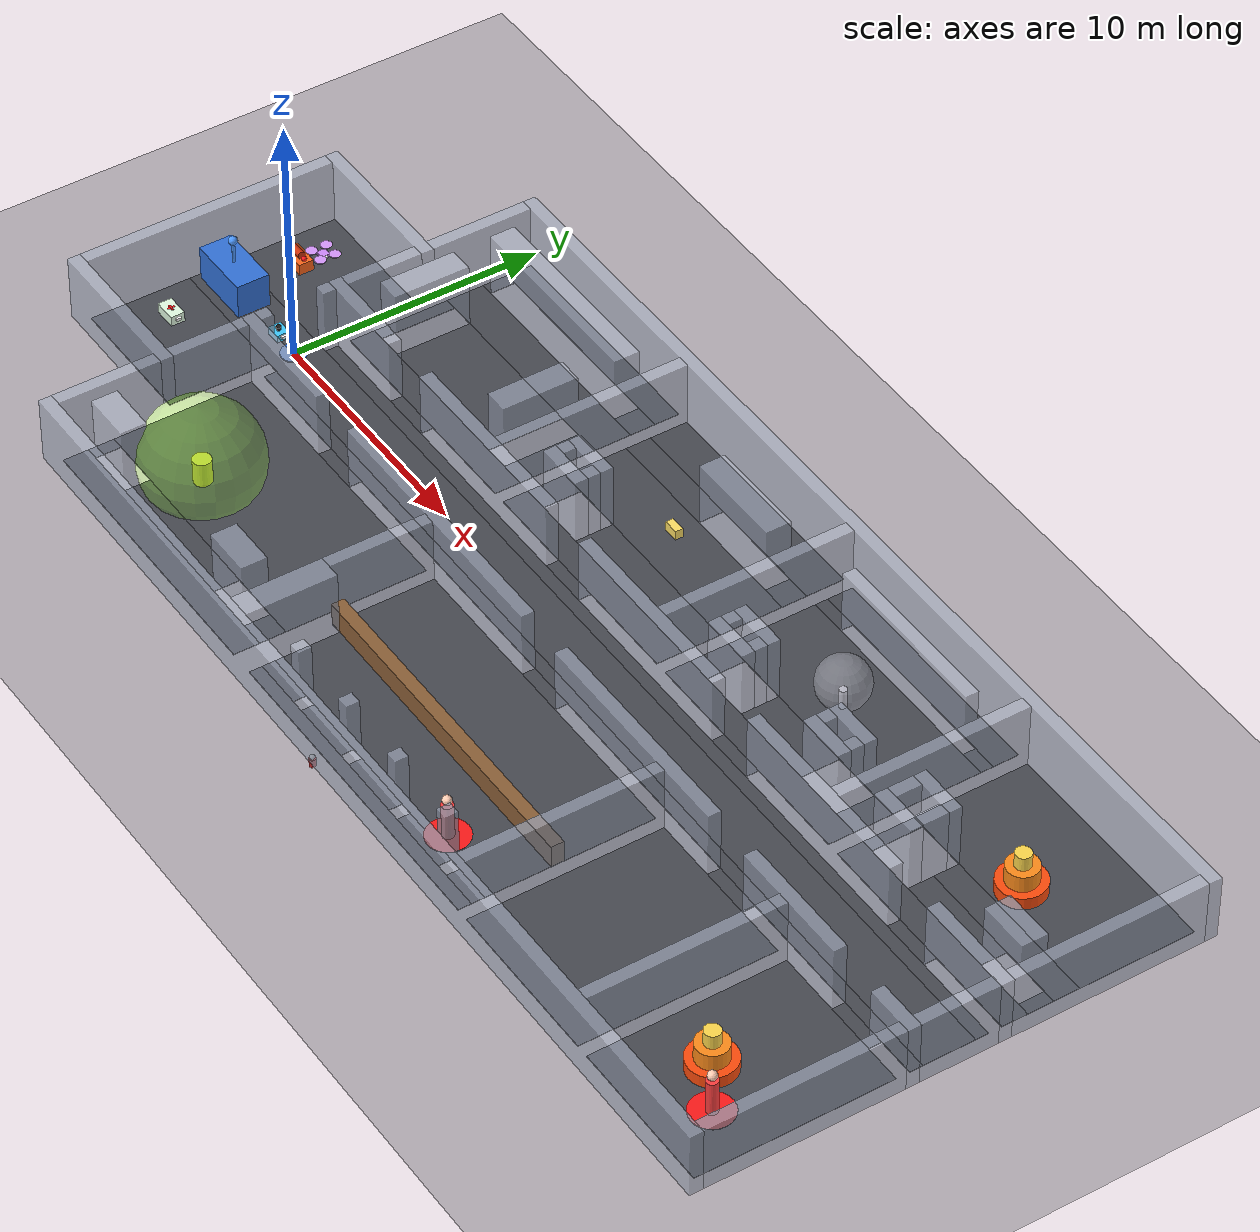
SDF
<?xml version="1.0" ?>
<sdf version="1.9">
<world name="living_map_fire">
<physics name="fast" type="ignored"><max_step_size>0.01</max_step_size><real_time_factor>1.0</real_time_factor></physics>
<plugin filename="gz-sim-physics-system" name="gz::sim::systems::Physics"/>
<plugin filename="gz-sim-user-commands-system" name="gz::sim::systems::UserCommands"/>
<plugin filename="gz-sim-scene-broadcaster-system" name="gz::sim::systems::SceneBroadcaster"/>
<scene><ambient>0.45 0.45 0.5 1</ambient><background>0.05 0.07 0.12 1</background><shadows>true</shadows></scene>
<gui fullscreen="0"><plugin filename="MinimalScene" name="3D View"><gz-gui><title>3D View</title><property type="bool" key="showTitleBar">false</property><property type="string" key="state">docked</property></gz-gui><engine>ogre2</engine><scene>scene</scene><ambient_light>0.4 0.4 0.4</ambient_light><background_color>0.05 0.07 0.12</background_color><camera_pose>18 -26 28 0 0.85 1.5708</camera_pose></plugin><plugin filename="GzSceneManager" name="Scene Manager"><gz-gui><property key="resizable" type="bool">false</property><property key="width" type="double">5</property><property key="height" type="double">5</property><property key="state" type="string">floating</property><property key="showTitleBar" type="bool">false</property></gz-gui></plugin><plugin filename="InteractiveViewControl" name="Interactive view control"><gz-gui><property key="resizable" type="bool">false</property><property key="width" type="double">5</property><property key="height" type="double">5</property><property key="state" type="string">floating</property><property key="showTitleBar" type="bool">false</property></gz-gui></plugin><plugin filename="WorldControl" name="World control"><gz-gui><title>World control</title><property type="bool" key="showTitleBar">false</property><property type="bool" key="resizable">false</property><property type="double" key="height">72</property><property type="double" key="width">121</property><property type="double" key="z">1</property><property type="string" key="state">floating</property><anchors target="3D View"><line own="left" target="left"/><line own="bottom" target="bottom"/></anchors></gz-gui><play_pause>true</play_pause><step>true</step><start_paused>false</start_paused></plugin><plugin filename="WorldStats" name="World stats"><gz-gui><title>World stats</title><property type="bool" key="showTitleBar">false</property><property type="bool" key="resizable">false</property><property type="double" key="height">110</property><property type="double" key="width">290</property><property type="double" key="z">1</property><property type="string" key="state">floating</property><anchors target="3D View"><line own="right" target="right"/><line own="bottom" target="bottom"/></anchors></gz-gui><sim_time>true</sim_time><real_time>true</real_time><real_time_factor>true</real_time_factor><iterations>true</iterations></plugin></gui>
<light type="directional" name="sun"><cast_shadows>true</cast_shadows><pose>0 0 10 0 0 0</pose><diffuse>0.9 0.9 0.9 1</diffuse><specular>0.2 0.2 0.2 1</specular><direction>-0.4 0.2 -0.9</direction></light>
<model name="ground"><static>true</static><link name="l"><collision name="c"><geometry><plane><normal>0 0 1</normal><size>120 80</size></plane></geometry></collision><visual name="v"><geometry><plane><normal>0 0 1</normal><size>120 80</size></plane></geometry><material><ambient>0.16 0.17 0.2 1.0</ambient><diffuse>0.16 0.17 0.2 1.0</diffuse></material></visual></link></model>
<model name="slab0_0"><static>true</static><pose>6.250 -9.000 0.010 0 0 0</pose><link name="l"><collision name="c"><geometry><box><size>11.500 1.000 0.020</size></box></geometry></collision><visual name="v"><geometry><box><size>11.500 1.000 0.020</size></box></geometry><material><ambient>0.28 0.29 0.32 1.0</ambient><diffuse>0.28 0.29 0.32 1.0</diffuse></material></visual></link></model>
<model name="slab0_1"><static>true</static><pose>19.500 -9.250 0.010 0 0 0</pose><link name="l"><collision name="c"><geometry><box><size>13.000 0.500 0.020</size></box></geometry></collision><visual name="v"><geometry><box><size>13.000 0.500 0.020</size></box></geometry><material><ambient>0.28 0.29 0.32 1.0</ambient><diffuse>0.28 0.29 0.32 1.0</diffuse></material></visual></link></model>
<model name="slab0_2"><static>true</static><pose>29.750 -5.750 0.010 0 0 0</pose><link name="l"><collision name="c"><geometry><box><size>6.500 7.500 0.020</size></box></geometry></collision><visual name="v"><geometry><box><size>6.500 7.500 0.020</size></box></geometry><material><ambient>0.28 0.29 0.32 1.0</ambient><diffuse>0.28 0.29 0.32 1.0</diffuse></material></visual></link></model>
<model name="slab0_3"><static>true</static><pose>36.500 -5.750 0.010 0 0 0</pose><link name="l"><collision name="c"><geometry><box><size>6.000 7.500 0.020</size></box></geometry></collision><visual name="v"><geometry><box><size>6.000 7.500 0.020</size></box></geometry><material><ambient>0.28 0.29 0.32 1.0</ambient><diffuse>0.28 0.29 0.32 1.0</diffuse></material></visual></link></model>
<model name="slab0_4"><static>true</static><pose>14.000 -8.750 0.010 0 0 0</pose><link name="l"><collision name="c"><geometry><box><size>2.000 0.500 0.020</size></box></geometry></collision><visual name="v"><geometry><box><size>2.000 0.500 0.020</size></box></geometry><material><ambient>0.28 0.29 0.32 1.0</ambient><diffuse>0.28 0.29 0.32 1.0</diffuse></material></visual></link></model>
<model name="slab0_5"><static>true</static><pose>16.750 -8.750 0.010 0 0 0</pose><link name="l"><collision name="c"><geometry><box><size>2.500 0.500 0.020</size></box></geometry></collision><visual name="v"><geometry><box><size>2.500 0.500 0.020</size></box></geometry><material><ambient>0.28 0.29 0.32 1.0</ambient><diffuse>0.28 0.29 0.32 1.0</diffuse></material></visual></link></model>
<model name="slab0_6"><static>true</static><pose>19.750 -8.750 0.010 0 0 0</pose><link name="l"><collision name="c"><geometry><box><size>2.500 0.500 0.020</size></box></geometry></collision><visual name="v"><geometry><box><size>2.500 0.500 0.020</size></box></geometry><material><ambient>0.28 0.29 0.32 1.0</ambient><diffuse>0.28 0.29 0.32 1.0</diffuse></material></visual></link></model>
<model name="slab0_7"><static>true</static><pose>22.750 -8.750 0.010 0 0 0</pose><link name="l"><collision name="c"><geometry><box><size>2.500 0.500 0.020</size></box></geometry></collision><visual name="v"><geometry><box><size>2.500 0.500 0.020</size></box></geometry><material><ambient>0.28 0.29 0.32 1.0</ambient><diffuse>0.28 0.29 0.32 1.0</diffuse></material></visual></link></model>
<model name="slab0_8"><static>true</static><pose>25.250 -8.750 0.010 0 0 0</pose><link name="l"><collision name="c"><geometry><box><size>1.500 0.500 0.020</size></box></geometry></collision><visual name="v"><geometry><box><size>1.500 0.500 0.020</size></box></geometry><material><ambient>0.28 0.29 0.32 1.0</ambient><diffuse>0.28 0.29 0.32 1.0</diffuse></material></visual></link></model>
<model name="slab0_9"><static>true</static><pose>0.750 -8.000 0.010 0 0 0</pose><link name="l"><collision name="c"><geometry><box><size>0.500 1.000 0.020</size></box></geometry></collision><visual name="v"><geometry><box><size>0.500 1.000 0.020</size></box></geometry><material><ambient>0.28 0.29 0.32 1.0</ambient><diffuse>0.28 0.29 0.32 1.0</diffuse></material></visual></link></model>
<model name="slab0_10"><static>true</static><pose>6.000 -8.000 0.010 0 0 0</pose><link name="l"><collision name="c"><geometry><box><size>6.000 1.000 0.020</size></box></geometry></collision><visual name="v"><geometry><box><size>6.000 1.000 0.020</size></box></geometry><material><ambient>0.28 0.29 0.32 1.0</ambient><diffuse>0.28 0.29 0.32 1.0</diffuse></material></visual></link></model>
<model name="slab0_11"><static>true</static><pose>11.500 -8.000 0.010 0 0 0</pose><link name="l"><collision name="c"><geometry><box><size>1.000 1.000 0.020</size></box></geometry></collision><visual name="v"><geometry><box><size>1.000 1.000 0.020</size></box></geometry><material><ambient>0.28 0.29 0.32 1.0</ambient><diffuse>0.28 0.29 0.32 1.0</diffuse></material></visual></link></model>
<model name="slab0_12"><static>true</static><pose>19.500 -7.250 0.010 0 0 0</pose><link name="l"><collision name="c"><geometry><box><size>13.000 2.500 0.020</size></box></geometry></collision><visual name="v"><geometry><box><size>13.000 2.500 0.020</size></box></geometry><material><ambient>0.28 0.29 0.32 1.0</ambient><diffuse>0.28 0.29 0.32 1.0</diffuse></material></visual></link></model>
<model name="slab0_13"><static>true</static><pose>6.250 -4.750 0.010 0 0 0</pose><link name="l"><collision name="c"><geometry><box><size>11.500 5.500 0.020</size></box></geometry></collision><visual name="v"><geometry><box><size>11.500 5.500 0.020</size></box></geometry><material><ambient>0.28 0.29 0.32 1.0</ambient><diffuse>0.28 0.29 0.32 1.0</diffuse></material></visual></link></model>
<model name="slab0_14"><static>true</static><pose>19.250 -4.000 0.010 0 0 0</pose><link name="l"><collision name="c"><geometry><box><size>13.500 4.000 0.020</size></box></geometry></collision><visual name="v"><geometry><box><size>13.500 4.000 0.020</size></box></geometry><material><ambient>0.28 0.29 0.32 1.0</ambient><diffuse>0.28 0.29 0.32 1.0</diffuse></material></visual></link></model>
<model name="slab0_15"><static>true</static><pose>-2.750 -3.000 0.010 0 0 0</pose><link name="l"><collision name="c"><geometry><box><size>5.500 4.000 0.020</size></box></geometry></collision><visual name="v"><geometry><box><size>5.500 4.000 0.020</size></box></geometry><material><ambient>0.28 0.29 0.32 1.0</ambient><diffuse>0.28 0.29 0.32 1.0</diffuse></material></visual></link></model>
<model name="slab0_16"><static>true</static><pose>6.000 -1.750 0.010 0 0 0</pose><link name="l"><collision name="c"><geometry><box><size>2.000 0.500 0.020</size></box></geometry></collision><visual name="v"><geometry><box><size>2.000 0.500 0.020</size></box></geometry><material><ambient>0.28 0.29 0.32 1.0</ambient><diffuse>0.28 0.29 0.32 1.0</diffuse></material></visual></link></model>
<model name="slab0_17"><static>true</static><pose>19.000 -1.750 0.010 0 0 0</pose><link name="l"><collision name="c"><geometry><box><size>2.000 0.500 0.020</size></box></geometry></collision><visual name="v"><geometry><box><size>2.000 0.500 0.020</size></box></geometry><material><ambient>0.28 0.29 0.32 1.0</ambient><diffuse>0.28 0.29 0.32 1.0</diffuse></material></visual></link></model>
<model name="slab0_18"><static>true</static><pose>30.000 -1.750 0.010 0 0 0</pose><link name="l"><collision name="c"><geometry><box><size>2.000 0.500 0.020</size></box></geometry></collision><visual name="v"><geometry><box><size>2.000 0.500 0.020</size></box></geometry><material><ambient>0.28 0.29 0.32 1.0</ambient><diffuse>0.28 0.29 0.32 1.0</diffuse></material></visual></link></model>
<model name="slab0_19"><static>true</static><pose>37.000 -1.750 0.010 0 0 0</pose><link name="l"><collision name="c"><geometry><box><size>2.000 0.500 0.020</size></box></geometry></collision><visual name="v"><geometry><box><size>2.000 0.500 0.020</size></box></geometry><material><ambient>0.28 0.29 0.32 1.0</ambient><diffuse>0.28 0.29 0.32 1.0</diffuse></material></visual></link></model>
<model name="slab0_20"><static>true</static><pose>20.000 -1.250 0.010 0 0 0</pose><link name="l"><collision name="c"><geometry><box><size>39.000 0.500 0.020</size></box></geometry></collision><visual name="v"><geometry><box><size>39.000 0.500 0.020</size></box></geometry><material><ambient>0.28 0.29 0.32 1.0</ambient><diffuse>0.28 0.29 0.32 1.0</diffuse></material></visual></link></model>
<model name="slab0_21"><static>true</static><pose>17.000 0.000 0.010 0 0 0</pose><link name="l"><collision name="c"><geometry><box><size>45.000 2.000 0.020</size></box></geometry></collision><visual name="v"><geometry><box><size>45.000 2.000 0.020</size></box></geometry><material><ambient>0.28 0.29 0.32 1.0</ambient><diffuse>0.28 0.29 0.32 1.0</diffuse></material></visual></link></model>
<model name="slab0_22"><static>true</static><pose>-2.750 3.000 0.010 0 0 0</pose><link name="l"><collision name="c"><geometry><box><size>5.500 4.000 0.020</size></box></geometry></collision><visual name="v"><geometry><box><size>5.500 4.000 0.020</size></box></geometry><material><ambient>0.28 0.29 0.32 1.0</ambient><diffuse>0.28 0.29 0.32 1.0</diffuse></material></visual></link></model>
<model name="slab0_23"><static>true</static><pose>20.000 1.250 0.010 0 0 0</pose><link name="l"><collision name="c"><geometry><box><size>39.000 0.500 0.020</size></box></geometry></collision><visual name="v"><geometry><box><size>39.000 0.500 0.020</size></box></geometry><material><ambient>0.28 0.29 0.32 1.0</ambient><diffuse>0.28 0.29 0.32 1.0</diffuse></material></visual></link></model>
<model name="slab0_24"><static>true</static><pose>5.000 1.750 0.010 0 0 0</pose><link name="l"><collision name="c"><geometry><box><size>2.000 0.500 0.020</size></box></geometry></collision><visual name="v"><geometry><box><size>2.000 0.500 0.020</size></box></geometry><material><ambient>0.28 0.29 0.32 1.0</ambient><diffuse>0.28 0.29 0.32 1.0</diffuse></material></visual></link></model>
<model name="slab0_25"><static>true</static><pose>15.000 1.750 0.010 0 0 0</pose><link name="l"><collision name="c"><geometry><box><size>2.000 0.500 0.020</size></box></geometry></collision><visual name="v"><geometry><box><size>2.000 0.500 0.020</size></box></geometry><material><ambient>0.28 0.29 0.32 1.0</ambient><diffuse>0.28 0.29 0.32 1.0</diffuse></material></visual></link></model>
<model name="slab0_26"><static>true</static><pose>25.000 1.750 0.010 0 0 0</pose><link name="l"><collision name="c"><geometry><box><size>2.000 0.500 0.020</size></box></geometry></collision><visual name="v"><geometry><box><size>2.000 0.500 0.020</size></box></geometry><material><ambient>0.28 0.29 0.32 1.0</ambient><diffuse>0.28 0.29 0.32 1.0</diffuse></material></visual></link></model>
<model name="slab0_27"><static>true</static><pose>35.000 1.750 0.010 0 0 0</pose><link name="l"><collision name="c"><geometry><box><size>2.000 0.500 0.020</size></box></geometry></collision><visual name="v"><geometry><box><size>2.000 0.500 0.020</size></box></geometry><material><ambient>0.28 0.29 0.32 1.0</ambient><diffuse>0.28 0.29 0.32 1.0</diffuse></material></visual></link></model>
<model name="slab0_28"><static>true</static><pose>5.250 2.500 0.010 0 0 0</pose><link name="l"><collision name="c"><geometry><box><size>9.500 1.000 0.020</size></box></geometry></collision><visual name="v"><geometry><box><size>9.500 1.000 0.020</size></box></geometry><material><ambient>0.28 0.29 0.32 1.0</ambient><diffuse>0.28 0.29 0.32 1.0</diffuse></material></visual></link></model>
<model name="slab0_29"><static>true</static><pose>15.250 2.500 0.010 0 0 0</pose><link name="l"><collision name="c"><geometry><box><size>9.500 1.000 0.020</size></box></geometry></collision><visual name="v"><geometry><box><size>9.500 1.000 0.020</size></box></geometry><material><ambient>0.28 0.29 0.32 1.0</ambient><diffuse>0.28 0.29 0.32 1.0</diffuse></material></visual></link></model>
<model name="slab0_30"><static>true</static><pose>25.250 2.500 0.010 0 0 0</pose><link name="l"><collision name="c"><geometry><box><size>9.500 1.000 0.020</size></box></geometry></collision><visual name="v"><geometry><box><size>9.500 1.000 0.020</size></box></geometry><material><ambient>0.28 0.29 0.32 1.0</ambient><diffuse>0.28 0.29 0.32 1.0</diffuse></material></visual></link></model>
<model name="slab0_31"><static>true</static><pose>35.000 2.500 0.010 0 0 0</pose><link name="l"><collision name="c"><geometry><box><size>9.000 1.000 0.020</size></box></geometry></collision><visual name="v"><geometry><box><size>9.000 1.000 0.020</size></box></geometry><material><ambient>0.28 0.29 0.32 1.0</ambient><diffuse>0.28 0.29 0.32 1.0</diffuse></material></visual></link></model>
<model name="slab0_32"><static>true</static><pose>0.750 4.500 0.010 0 0 0</pose><link name="l"><collision name="c"><geometry><box><size>0.500 3.000 0.020</size></box></geometry></collision><visual name="v"><geometry><box><size>0.500 3.000 0.020</size></box></geometry><material><ambient>0.28 0.29 0.32 1.0</ambient><diffuse>0.28 0.29 0.32 1.0</diffuse></material></visual></link></model>
<model name="slab0_33"><static>true</static><pose>5.000 4.500 0.010 0 0 0</pose><link name="l"><collision name="c"><geometry><box><size>6.000 3.000 0.020</size></box></geometry></collision><visual name="v"><geometry><box><size>6.000 3.000 0.020</size></box></geometry><material><ambient>0.28 0.29 0.32 1.0</ambient><diffuse>0.28 0.29 0.32 1.0</diffuse></material></visual></link></model>
<model name="slab0_34"><static>true</static><pose>9.500 4.500 0.010 0 0 0</pose><link name="l"><collision name="c"><geometry><box><size>1.000 3.000 0.020</size></box></geometry></collision><visual name="v"><geometry><box><size>1.000 3.000 0.020</size></box></geometry><material><ambient>0.28 0.29 0.32 1.0</ambient><diffuse>0.28 0.29 0.32 1.0</diffuse></material></visual></link></model>
<model name="slab0_35"><static>true</static><pose>11.000 3.750 0.010 0 0 0</pose><link name="l"><collision name="c"><geometry><box><size>1.000 1.500 0.020</size></box></geometry></collision><visual name="v"><geometry><box><size>1.000 1.500 0.020</size></box></geometry><material><ambient>0.28 0.29 0.32 1.0</ambient><diffuse>0.28 0.29 0.32 1.0</diffuse></material></visual></link></model>
<model name="slab0_36"><static>true</static><pose>16.750 3.750 0.010 0 0 0</pose><link name="l"><collision name="c"><geometry><box><size>6.500 1.500 0.020</size></box></geometry></collision><visual name="v"><geometry><box><size>6.500 1.500 0.020</size></box></geometry><material><ambient>0.28 0.29 0.32 1.0</ambient><diffuse>0.28 0.29 0.32 1.0</diffuse></material></visual></link></model>
<model name="slab0_37"><static>true</static><pose>21.000 3.750 0.010 0 0 0</pose><link name="l"><collision name="c"><geometry><box><size>1.000 1.500 0.020</size></box></geometry></collision><visual name="v"><geometry><box><size>1.000 1.500 0.020</size></box></geometry><material><ambient>0.28 0.29 0.32 1.0</ambient><diffuse>0.28 0.29 0.32 1.0</diffuse></material></visual></link></model>
<model name="slab0_38"><static>true</static><pose>25.250 3.750 0.010 0 0 0</pose><link name="l"><collision name="c"><geometry><box><size>3.500 1.500 0.020</size></box></geometry></collision><visual name="v"><geometry><box><size>3.500 1.500 0.020</size></box></geometry><material><ambient>0.28 0.29 0.32 1.0</ambient><diffuse>0.28 0.29 0.32 1.0</diffuse></material></visual></link></model>
<model name="slab0_39"><static>true</static><pose>29.500 3.750 0.010 0 0 0</pose><link name="l"><collision name="c"><geometry><box><size>1.000 1.500 0.020</size></box></geometry></collision><visual name="v"><geometry><box><size>1.000 1.500 0.020</size></box></geometry><material><ambient>0.28 0.29 0.32 1.0</ambient><diffuse>0.28 0.29 0.32 1.0</diffuse></material></visual></link></model>
<model name="slab0_40"><static>true</static><pose>30.750 4.000 0.010 0 0 0</pose><link name="l"><collision name="c"><geometry><box><size>0.500 2.000 0.020</size></box></geometry></collision><visual name="v"><geometry><box><size>0.500 2.000 0.020</size></box></geometry><material><ambient>0.28 0.29 0.32 1.0</ambient><diffuse>0.28 0.29 0.32 1.0</diffuse></material></visual></link></model>
<model name="slab0_41"><static>true</static><pose>35.000 3.500 0.010 0 0 0</pose><link name="l"><collision name="c"><geometry><box><size>4.000 1.000 0.020</size></box></geometry></collision><visual name="v"><geometry><box><size>4.000 1.000 0.020</size></box></geometry><material><ambient>0.28 0.29 0.32 1.0</ambient><diffuse>0.28 0.29 0.32 1.0</diffuse></material></visual></link></model>
<model name="slab0_42"><static>true</static><pose>39.250 3.500 0.010 0 0 0</pose><link name="l"><collision name="c"><geometry><box><size>0.500 1.000 0.020</size></box></geometry></collision><visual name="v"><geometry><box><size>0.500 1.000 0.020</size></box></geometry><material><ambient>0.28 0.29 0.32 1.0</ambient><diffuse>0.28 0.29 0.32 1.0</diffuse></material></visual></link></model>
<model name="slab0_43"><static>true</static><pose>36.250 4.500 0.010 0 0 0</pose><link name="l"><collision name="c"><geometry><box><size>6.500 1.000 0.020</size></box></geometry></collision><visual name="v"><geometry><box><size>6.500 1.000 0.020</size></box></geometry><material><ambient>0.28 0.29 0.32 1.0</ambient><diffuse>0.28 0.29 0.32 1.0</diffuse></material></visual></link></model>
<model name="slab0_44"><static>true</static><pose>15.250 5.750 0.010 0 0 0</pose><link name="l"><collision name="c"><geometry><box><size>9.500 2.500 0.020</size></box></geometry></collision><visual name="v"><geometry><box><size>9.500 2.500 0.020</size></box></geometry><material><ambient>0.28 0.29 0.32 1.0</ambient><diffuse>0.28 0.29 0.32 1.0</diffuse></material></visual></link></model>
<model name="slab0_45"><static>true</static><pose>25.250 6.250 0.010 0 0 0</pose><link name="l"><collision name="c"><geometry><box><size>9.500 3.500 0.020</size></box></geometry></collision><visual name="v"><geometry><box><size>9.500 3.500 0.020</size></box></geometry><material><ambient>0.28 0.29 0.32 1.0</ambient><diffuse>0.28 0.29 0.32 1.0</diffuse></material></visual></link></model>
<model name="slab0_46"><static>true</static><pose>35.000 7.250 0.010 0 0 0</pose><link name="l"><collision name="c"><geometry><box><size>9.000 4.500 0.020</size></box></geometry></collision><visual name="v"><geometry><box><size>9.000 4.500 0.020</size></box></geometry><material><ambient>0.28 0.29 0.32 1.0</ambient><diffuse>0.28 0.29 0.32 1.0</diffuse></material></visual></link></model>
<model name="slab0_47"><static>true</static><pose>5.250 6.750 0.010 0 0 0</pose><link name="l"><collision name="c"><geometry><box><size>9.500 1.500 0.020</size></box></geometry></collision><visual name="v"><geometry><box><size>9.500 1.500 0.020</size></box></geometry><material><ambient>0.28 0.29 0.32 1.0</ambient><diffuse>0.28 0.29 0.32 1.0</diffuse></material></visual></link></model>
<model name="slab0_48"><static>true</static><pose>12.750 7.500 0.010 0 0 0</pose><link name="l"><collision name="c"><geometry><box><size>4.500 1.000 0.020</size></box></geometry></collision><visual name="v"><geometry><box><size>4.500 1.000 0.020</size></box></geometry><material><ambient>0.28 0.29 0.32 1.0</ambient><diffuse>0.28 0.29 0.32 1.0</diffuse></material></visual></link></model>
<model name="slab0_49"><static>true</static><pose>19.500 7.500 0.010 0 0 0</pose><link name="l"><collision name="c"><geometry><box><size>1.000 1.000 0.020</size></box></geometry></collision><visual name="v"><geometry><box><size>1.000 1.000 0.020</size></box></geometry><material><ambient>0.28 0.29 0.32 1.0</ambient><diffuse>0.28 0.29 0.32 1.0</diffuse></material></visual></link></model>
<model name="slab0_50"><static>true</static><pose>0.750 8.000 0.010 0 0 0</pose><link name="l"><collision name="c"><geometry><box><size>0.500 1.000 0.020</size></box></geometry></collision><visual name="v"><geometry><box><size>0.500 1.000 0.020</size></box></geometry><material><ambient>0.28 0.29 0.32 1.0</ambient><diffuse>0.28 0.29 0.32 1.0</diffuse></material></visual></link></model>
<model name="slab0_51"><static>true</static><pose>9.500 8.000 0.010 0 0 0</pose><link name="l"><collision name="c"><geometry><box><size>1.000 1.000 0.020</size></box></geometry></collision><visual name="v"><geometry><box><size>1.000 1.000 0.020</size></box></geometry><material><ambient>0.28 0.29 0.32 1.0</ambient><diffuse>0.28 0.29 0.32 1.0</diffuse></material></visual></link></model>
<model name="slab0_52"><static>true</static><pose>15.250 8.750 0.010 0 0 0</pose><link name="l"><collision name="c"><geometry><box><size>9.500 1.500 0.020</size></box></geometry></collision><visual name="v"><geometry><box><size>9.500 1.500 0.020</size></box></geometry><material><ambient>0.28 0.29 0.32 1.0</ambient><diffuse>0.28 0.29 0.32 1.0</diffuse></material></visual></link></model>
<model name="slab0_53"><static>true</static><pose>21.250 8.250 0.010 0 0 0</pose><link name="l"><collision name="c"><geometry><box><size>1.500 0.500 0.020</size></box></geometry></collision><visual name="v"><geometry><box><size>1.500 0.500 0.020</size></box></geometry><material><ambient>0.28 0.29 0.32 1.0</ambient><diffuse>0.28 0.29 0.32 1.0</diffuse></material></visual></link></model>
<model name="slab0_54"><static>true</static><pose>29.500 8.250 0.010 0 0 0</pose><link name="l"><collision name="c"><geometry><box><size>1.000 0.500 0.020</size></box></geometry></collision><visual name="v"><geometry><box><size>1.000 0.500 0.020</size></box></geometry><material><ambient>0.28 0.29 0.32 1.0</ambient><diffuse>0.28 0.29 0.32 1.0</diffuse></material></visual></link></model>
<model name="slab0_55"><static>true</static><pose>5.250 9.000 0.010 0 0 0</pose><link name="l"><collision name="c"><geometry><box><size>9.500 1.000 0.020</size></box></geometry></collision><visual name="v"><geometry><box><size>9.500 1.000 0.020</size></box></geometry><material><ambient>0.28 0.29 0.32 1.0</ambient><diffuse>0.28 0.29 0.32 1.0</diffuse></material></visual></link></model>
<model name="slab0_56"><static>true</static><pose>25.250 9.000 0.010 0 0 0</pose><link name="l"><collision name="c"><geometry><box><size>9.500 1.000 0.020</size></box></geometry></collision><visual name="v"><geometry><box><size>9.500 1.000 0.020</size></box></geometry><material><ambient>0.28 0.29 0.32 1.0</ambient><diffuse>0.28 0.29 0.32 1.0</diffuse></material></visual></link></model>
<model name="wall0_0"><static>true</static><pose>20.000 -9.750 1.300 0 0 0</pose><link name="l"><collision name="c"><geometry><box><size>40.000 0.500 2.600</size></box></geometry></collision><visual name="v"><geometry><box><size>40.000 0.500 2.600</size></box></geometry><material><ambient>0.62 0.65 0.72 0.75</ambient><diffuse>0.62 0.65 0.72 0.75</diffuse></material></visual></link></model>
<model name="wall0_1"><static>true</static><pose>0.250 -7.500 1.300 0 0 0</pose><link name="l"><collision name="c"><geometry><box><size>0.500 4.000 2.600</size></box></geometry></collision><visual name="v"><geometry><box><size>0.500 4.000 2.600</size></box></geometry><material><ambient>0.62 0.65 0.72 0.75</ambient><diffuse>0.62 0.65 0.72 0.75</diffuse></material></visual></link></model>
<model name="wall0_2"><static>true</static><pose>12.500 -7.750 1.300 0 0 0</pose><link name="l"><collision name="c"><geometry><box><size>1.000 3.500 2.600</size></box></geometry></collision><visual name="v"><geometry><box><size>1.000 3.500 2.600</size></box></geometry><material><ambient>0.62 0.65 0.72 0.75</ambient><diffuse>0.62 0.65 0.72 0.75</diffuse></material></visual></link></model>
<model name="wall0_3"><static>true</static><pose>26.250 -5.750 1.300 0 0 0</pose><link name="l"><collision name="c"><geometry><box><size>0.500 7.500 2.600</size></box></geometry></collision><visual name="v"><geometry><box><size>0.500 7.500 2.600</size></box></geometry><material><ambient>0.62 0.65 0.72 0.75</ambient><diffuse>0.62 0.65 0.72 0.75</diffuse></material></visual></link></model>
<model name="wall0_4"><static>true</static><pose>33.250 -5.750 1.300 0 0 0</pose><link name="l"><collision name="c"><geometry><box><size>0.500 7.500 2.600</size></box></geometry></collision><visual name="v"><geometry><box><size>0.500 7.500 2.600</size></box></geometry><material><ambient>0.62 0.65 0.72 0.75</ambient><diffuse>0.62 0.65 0.72 0.75</diffuse></material></visual></link></model>
<model name="wall0_5"><static>true</static><pose>39.750 -5.750 1.300 0 0 0</pose><link name="l"><collision name="c"><geometry><box><size>0.500 7.500 2.600</size></box></geometry></collision><visual name="v"><geometry><box><size>0.500 7.500 2.600</size></box></geometry><material><ambient>0.62 0.65 0.72 0.75</ambient><diffuse>0.62 0.65 0.72 0.75</diffuse></material></visual></link></model>
<model name="wall0_6"><static>true</static><pose>15.250 -8.750 1.300 0 0 0</pose><link name="l"><collision name="c"><geometry><box><size>0.500 0.500 2.600</size></box></geometry></collision><visual name="v"><geometry><box><size>0.500 0.500 2.600</size></box></geometry><material><ambient>0.62 0.65 0.72 0.75</ambient><diffuse>0.62 0.65 0.72 0.75</diffuse></material></visual></link></model>
<model name="wall0_7"><static>true</static><pose>18.250 -8.750 1.300 0 0 0</pose><link name="l"><collision name="c"><geometry><box><size>0.500 0.500 2.600</size></box></geometry></collision><visual name="v"><geometry><box><size>0.500 0.500 2.600</size></box></geometry><material><ambient>0.62 0.65 0.72 0.75</ambient><diffuse>0.62 0.65 0.72 0.75</diffuse></material></visual></link></model>
<model name="wall0_8"><static>true</static><pose>21.250 -8.750 1.300 0 0 0</pose><link name="l"><collision name="c"><geometry><box><size>0.500 0.500 2.600</size></box></geometry></collision><visual name="v"><geometry><box><size>0.500 0.500 2.600</size></box></geometry><material><ambient>0.62 0.65 0.72 0.75</ambient><diffuse>0.62 0.65 0.72 0.75</diffuse></material></visual></link></model>
<model name="wall0_9"><static>true</static><pose>24.250 -8.750 1.300 0 0 0</pose><link name="l"><collision name="c"><geometry><box><size>0.500 0.500 2.600</size></box></geometry></collision><visual name="v"><geometry><box><size>0.500 0.500 2.600</size></box></geometry><material><ambient>0.62 0.65 0.72 0.75</ambient><diffuse>0.62 0.65 0.72 0.75</diffuse></material></visual></link></model>
<model name="wall0_10"><static>true</static><pose>2.000 -8.000 1.300 0 0 0</pose><link name="l"><collision name="c"><geometry><box><size>2.000 1.000 2.600</size></box></geometry></collision><visual name="v"><geometry><box><size>2.000 1.000 2.600</size></box></geometry><material><ambient>0.62 0.65 0.72 0.75</ambient><diffuse>0.62 0.65 0.72 0.75</diffuse></material></visual></link></model>
<model name="wall0_11"><static>true</static><pose>10.000 -8.000 1.300 0 0 0</pose><link name="l"><collision name="c"><geometry><box><size>2.000 1.000 2.600</size></box></geometry></collision><visual name="v"><geometry><box><size>2.000 1.000 2.600</size></box></geometry><material><ambient>0.62 0.65 0.72 0.75</ambient><diffuse>0.62 0.65 0.72 0.75</diffuse></material></visual></link></model>
<model name="wall0_12"><static>true</static><pose>12.250 -4.000 1.300 0 0 0</pose><link name="l"><collision name="c"><geometry><box><size>0.500 4.000 2.600</size></box></geometry></collision><visual name="v"><geometry><box><size>0.500 4.000 2.600</size></box></geometry><material><ambient>0.62 0.65 0.72 0.75</ambient><diffuse>0.62 0.65 0.72 0.75</diffuse></material></visual></link></model>
<model name="wall0_13"><static>true</static><pose>-2.750 -5.250 1.300 0 0 0</pose><link name="l"><collision name="c"><geometry><box><size>6.500 0.500 2.600</size></box></geometry></collision><visual name="v"><geometry><box><size>6.500 0.500 2.600</size></box></geometry><material><ambient>0.62 0.65 0.72 0.75</ambient><diffuse>0.62 0.65 0.72 0.75</diffuse></material></visual></link></model>
<model name="wall0_14"><static>true</static><pose>-5.750 0.000 1.300 0 0 0</pose><link name="l"><collision name="c"><geometry><box><size>0.500 10.000 2.600</size></box></geometry></collision><visual name="v"><geometry><box><size>0.500 10.000 2.600</size></box></geometry><material><ambient>0.62 0.65 0.72 0.75</ambient><diffuse>0.62 0.65 0.72 0.75</diffuse></material></visual></link></model>
<model name="wall0_15"><static>true</static><pose>0.250 -3.500 1.300 0 0 0</pose><link name="l"><collision name="c"><geometry><box><size>0.500 3.000 2.600</size></box></geometry></collision><visual name="v"><geometry><box><size>0.500 3.000 2.600</size></box></geometry><material><ambient>0.62 0.65 0.72 0.75</ambient><diffuse>0.62 0.65 0.72 0.75</diffuse></material></visual></link></model>
<model name="wall0_16"><static>true</static><pose>2.500 -1.750 1.300 0 0 0</pose><link name="l"><collision name="c"><geometry><box><size>5.000 0.500 2.600</size></box></geometry></collision><visual name="v"><geometry><box><size>5.000 0.500 2.600</size></box></geometry><material><ambient>0.62 0.65 0.72 0.75</ambient><diffuse>0.62 0.65 0.72 0.75</diffuse></material></visual></link></model>
<model name="wall0_17"><static>true</static><pose>12.500 -1.750 1.300 0 0 0</pose><link name="l"><collision name="c"><geometry><box><size>11.000 0.500 2.600</size></box></geometry></collision><visual name="v"><geometry><box><size>11.000 0.500 2.600</size></box></geometry><material><ambient>0.62 0.65 0.72 0.75</ambient><diffuse>0.62 0.65 0.72 0.75</diffuse></material></visual></link></model>
<model name="wall0_18"><static>true</static><pose>24.500 -1.750 1.300 0 0 0</pose><link name="l"><collision name="c"><geometry><box><size>9.000 0.500 2.600</size></box></geometry></collision><visual name="v"><geometry><box><size>9.000 0.500 2.600</size></box></geometry><material><ambient>0.62 0.65 0.72 0.75</ambient><diffuse>0.62 0.65 0.72 0.75</diffuse></material></visual></link></model>
<model name="wall0_19"><static>true</static><pose>33.500 -1.750 1.300 0 0 0</pose><link name="l"><collision name="c"><geometry><box><size>5.000 0.500 2.600</size></box></geometry></collision><visual name="v"><geometry><box><size>5.000 0.500 2.600</size></box></geometry><material><ambient>0.62 0.65 0.72 0.75</ambient><diffuse>0.62 0.65 0.72 0.75</diffuse></material></visual></link></model>
<model name="wall0_20"><static>true</static><pose>39.000 -1.750 1.300 0 0 0</pose><link name="l"><collision name="c"><geometry><box><size>2.000 0.500 2.600</size></box></geometry></collision><visual name="v"><geometry><box><size>2.000 0.500 2.600</size></box></geometry><material><ambient>0.62 0.65 0.72 0.75</ambient><diffuse>0.62 0.65 0.72 0.75</diffuse></material></visual></link></model>
<model name="wall0_21"><static>true</static><pose>0.250 -1.250 1.300 0 0 0</pose><link name="l"><collision name="c"><geometry><box><size>0.500 0.500 2.600</size></box></geometry></collision><visual name="v"><geometry><box><size>0.500 0.500 2.600</size></box></geometry><material><ambient>0.62 0.65 0.72 0.75</ambient><diffuse>0.62 0.65 0.72 0.75</diffuse></material></visual></link></model>
<model name="wall0_22"><static>true</static><pose>39.750 0.000 1.300 0 0 0</pose><link name="l"><collision name="c"><geometry><box><size>0.500 3.000 2.600</size></box></geometry></collision><visual name="v"><geometry><box><size>0.500 3.000 2.600</size></box></geometry><material><ambient>0.62 0.65 0.72 0.75</ambient><diffuse>0.62 0.65 0.72 0.75</diffuse></material></visual></link></model>
<model name="wall0_23"><static>true</static><pose>0.250 1.250 1.300 0 0 0</pose><link name="l"><collision name="c"><geometry><box><size>0.500 0.500 2.600</size></box></geometry></collision><visual name="v"><geometry><box><size>0.500 0.500 2.600</size></box></geometry><material><ambient>0.62 0.65 0.72 0.75</ambient><diffuse>0.62 0.65 0.72 0.75</diffuse></material></visual></link></model>
<model name="wall0_24"><static>true</static><pose>2.000 1.750 1.300 0 0 0</pose><link name="l"><collision name="c"><geometry><box><size>4.000 0.500 2.600</size></box></geometry></collision><visual name="v"><geometry><box><size>4.000 0.500 2.600</size></box></geometry><material><ambient>0.62 0.65 0.72 0.75</ambient><diffuse>0.62 0.65 0.72 0.75</diffuse></material></visual></link></model>
<model name="wall0_25"><static>true</static><pose>10.000 1.750 1.300 0 0 0</pose><link name="l"><collision name="c"><geometry><box><size>8.000 0.500 2.600</size></box></geometry></collision><visual name="v"><geometry><box><size>8.000 0.500 2.600</size></box></geometry><material><ambient>0.62 0.65 0.72 0.75</ambient><diffuse>0.62 0.65 0.72 0.75</diffuse></material></visual></link></model>
<model name="wall0_26"><static>true</static><pose>20.000 1.750 1.300 0 0 0</pose><link name="l"><collision name="c"><geometry><box><size>8.000 0.500 2.600</size></box></geometry></collision><visual name="v"><geometry><box><size>8.000 0.500 2.600</size></box></geometry><material><ambient>0.62 0.65 0.72 0.75</ambient><diffuse>0.62 0.65 0.72 0.75</diffuse></material></visual></link></model>
<model name="wall0_27"><static>true</static><pose>30.000 1.750 1.300 0 0 0</pose><link name="l"><collision name="c"><geometry><box><size>8.000 0.500 2.600</size></box></geometry></collision><visual name="v"><geometry><box><size>8.000 0.500 2.600</size></box></geometry><material><ambient>0.62 0.65 0.72 0.75</ambient><diffuse>0.62 0.65 0.72 0.75</diffuse></material></visual></link></model>
<model name="wall0_28"><static>true</static><pose>38.000 1.750 1.300 0 0 0</pose><link name="l"><collision name="c"><geometry><box><size>4.000 0.500 2.600</size></box></geometry></collision><visual name="v"><geometry><box><size>4.000 0.500 2.600</size></box></geometry><material><ambient>0.62 0.65 0.72 0.75</ambient><diffuse>0.62 0.65 0.72 0.75</diffuse></material></visual></link></model>
<model name="wall0_29"><static>true</static><pose>0.250 3.500 1.300 0 0 0</pose><link name="l"><collision name="c"><geometry><box><size>0.500 3.000 2.600</size></box></geometry></collision><visual name="v"><geometry><box><size>0.500 3.000 2.600</size></box></geometry><material><ambient>0.62 0.65 0.72 0.75</ambient><diffuse>0.62 0.65 0.72 0.75</diffuse></material></visual></link></model>
<model name="wall0_30"><static>true</static><pose>10.250 5.750 1.300 0 0 0</pose><link name="l"><collision name="c"><geometry><box><size>0.500 7.500 2.600</size></box></geometry></collision><visual name="v"><geometry><box><size>0.500 7.500 2.600</size></box></geometry><material><ambient>0.62 0.65 0.72 0.75</ambient><diffuse>0.62 0.65 0.72 0.75</diffuse></material></visual></link></model>
<model name="wall0_31"><static>true</static><pose>20.250 5.750 1.300 0 0 0</pose><link name="l"><collision name="c"><geometry><box><size>0.500 7.500 2.600</size></box></geometry></collision><visual name="v"><geometry><box><size>0.500 7.500 2.600</size></box></geometry><material><ambient>0.62 0.65 0.72 0.75</ambient><diffuse>0.62 0.65 0.72 0.75</diffuse></material></visual></link></model>
<model name="wall0_32"><static>true</static><pose>30.250 5.750 1.300 0 0 0</pose><link name="l"><collision name="c"><geometry><box><size>0.500 7.500 2.600</size></box></geometry></collision><visual name="v"><geometry><box><size>0.500 7.500 2.600</size></box></geometry><material><ambient>0.62 0.65 0.72 0.75</ambient><diffuse>0.62 0.65 0.72 0.75</diffuse></material></visual></link></model>
<model name="wall0_33"><static>true</static><pose>39.750 5.750 1.300 0 0 0</pose><link name="l"><collision name="c"><geometry><box><size>0.500 7.500 2.600</size></box></geometry></collision><visual name="v"><geometry><box><size>0.500 7.500 2.600</size></box></geometry><material><ambient>0.62 0.65 0.72 0.75</ambient><diffuse>0.62 0.65 0.72 0.75</diffuse></material></visual></link></model>
<model name="wall0_34"><static>true</static><pose>1.500 4.500 1.300 0 0 0</pose><link name="l"><collision name="c"><geometry><box><size>1.000 3.000 2.600</size></box></geometry></collision><visual name="v"><geometry><box><size>1.000 3.000 2.600</size></box></geometry><material><ambient>0.62 0.65 0.72 0.75</ambient><diffuse>0.62 0.65 0.72 0.75</diffuse></material></visual></link></model>
<model name="wall0_35"><static>true</static><pose>8.500 4.500 1.300 0 0 0</pose><link name="l"><collision name="c"><geometry><box><size>1.000 3.000 2.600</size></box></geometry></collision><visual name="v"><geometry><box><size>1.000 3.000 2.600</size></box></geometry><material><ambient>0.62 0.65 0.72 0.75</ambient><diffuse>0.62 0.65 0.72 0.75</diffuse></material></visual></link></model>
<model name="wall0_36"><static>true</static><pose>12.500 3.250 1.300 0 0 0</pose><link name="l"><collision name="c"><geometry><box><size>2.000 0.500 2.600</size></box></geometry></collision><visual name="v"><geometry><box><size>2.000 0.500 2.600</size></box></geometry><material><ambient>0.62 0.65 0.72 0.75</ambient><diffuse>0.62 0.65 0.72 0.75</diffuse></material></visual></link></model>
<model name="wall0_37"><static>true</static><pose>22.500 3.250 1.300 0 0 0</pose><link name="l"><collision name="c"><geometry><box><size>2.000 0.500 2.600</size></box></geometry></collision><visual name="v"><geometry><box><size>2.000 0.500 2.600</size></box></geometry><material><ambient>0.62 0.65 0.72 0.75</ambient><diffuse>0.62 0.65 0.72 0.75</diffuse></material></visual></link></model>
<model name="wall0_38"><static>true</static><pose>28.000 3.250 1.300 0 0 0</pose><link name="l"><collision name="c"><geometry><box><size>2.000 0.500 2.600</size></box></geometry></collision><visual name="v"><geometry><box><size>2.000 0.500 2.600</size></box></geometry><material><ambient>0.62 0.65 0.72 0.75</ambient><diffuse>0.62 0.65 0.72 0.75</diffuse></material></visual></link></model>
<model name="wall0_39"><static>true</static><pose>32.000 3.250 1.300 0 0 0</pose><link name="l"><collision name="c"><geometry><box><size>2.000 0.500 2.600</size></box></geometry></collision><visual name="v"><geometry><box><size>2.000 0.500 2.600</size></box></geometry><material><ambient>0.62 0.65 0.72 0.75</ambient><diffuse>0.62 0.65 0.72 0.75</diffuse></material></visual></link></model>
<model name="wall0_40"><static>true</static><pose>38.000 3.500 1.300 0 0 0</pose><link name="l"><collision name="c"><geometry><box><size>2.000 1.000 2.600</size></box></geometry></collision><visual name="v"><geometry><box><size>2.000 1.000 2.600</size></box></geometry><material><ambient>0.62 0.65 0.72 0.75</ambient><diffuse>0.62 0.65 0.72 0.75</diffuse></material></visual></link></model>
<model name="wall0_41"><static>true</static><pose>11.750 3.750 1.300 0 0 0</pose><link name="l"><collision name="c"><geometry><box><size>0.500 0.500 2.600</size></box></geometry></collision><visual name="v"><geometry><box><size>0.500 0.500 2.600</size></box></geometry><material><ambient>0.62 0.65 0.72 0.75</ambient><diffuse>0.62 0.65 0.72 0.75</diffuse></material></visual></link></model>
<model name="wall0_42"><static>true</static><pose>13.250 3.750 1.300 0 0 0</pose><link name="l"><collision name="c"><geometry><box><size>0.500 0.500 2.600</size></box></geometry></collision><visual name="v"><geometry><box><size>0.500 0.500 2.600</size></box></geometry><material><ambient>0.62 0.65 0.72 0.75</ambient><diffuse>0.62 0.65 0.72 0.75</diffuse></material></visual></link></model>
<model name="wall0_43"><static>true</static><pose>21.750 3.750 1.300 0 0 0</pose><link name="l"><collision name="c"><geometry><box><size>0.500 0.500 2.600</size></box></geometry></collision><visual name="v"><geometry><box><size>0.500 0.500 2.600</size></box></geometry><material><ambient>0.62 0.65 0.72 0.75</ambient><diffuse>0.62 0.65 0.72 0.75</diffuse></material></visual></link></model>
<model name="wall0_44"><static>true</static><pose>23.250 3.750 1.300 0 0 0</pose><link name="l"><collision name="c"><geometry><box><size>0.500 0.500 2.600</size></box></geometry></collision><visual name="v"><geometry><box><size>0.500 0.500 2.600</size></box></geometry><material><ambient>0.62 0.65 0.72 0.75</ambient><diffuse>0.62 0.65 0.72 0.75</diffuse></material></visual></link></model>
<model name="wall0_45"><static>true</static><pose>27.250 3.750 1.300 0 0 0</pose><link name="l"><collision name="c"><geometry><box><size>0.500 0.500 2.600</size></box></geometry></collision><visual name="v"><geometry><box><size>0.500 0.500 2.600</size></box></geometry><material><ambient>0.62 0.65 0.72 0.75</ambient><diffuse>0.62 0.65 0.72 0.75</diffuse></material></visual></link></model>
<model name="wall0_46"><static>true</static><pose>28.750 3.750 1.300 0 0 0</pose><link name="l"><collision name="c"><geometry><box><size>0.500 0.500 2.600</size></box></geometry></collision><visual name="v"><geometry><box><size>0.500 0.500 2.600</size></box></geometry><material><ambient>0.62 0.65 0.72 0.75</ambient><diffuse>0.62 0.65 0.72 0.75</diffuse></material></visual></link></model>
<model name="wall0_47"><static>true</static><pose>31.250 4.000 1.300 0 0 0</pose><link name="l"><collision name="c"><geometry><box><size>0.500 1.000 2.600</size></box></geometry></collision><visual name="v"><geometry><box><size>0.500 1.000 2.600</size></box></geometry><material><ambient>0.62 0.65 0.72 0.75</ambient><diffuse>0.62 0.65 0.72 0.75</diffuse></material></visual></link></model>
<model name="wall0_48"><static>true</static><pose>32.750 4.000 1.300 0 0 0</pose><link name="l"><collision name="c"><geometry><box><size>0.500 1.000 2.600</size></box></geometry></collision><visual name="v"><geometry><box><size>0.500 1.000 2.600</size></box></geometry><material><ambient>0.62 0.65 0.72 0.75</ambient><diffuse>0.62 0.65 0.72 0.75</diffuse></material></visual></link></model>
<model name="wall0_49"><static>true</static><pose>12.500 4.250 1.300 0 0 0</pose><link name="l"><collision name="c"><geometry><box><size>2.000 0.500 2.600</size></box></geometry></collision><visual name="v"><geometry><box><size>2.000 0.500 2.600</size></box></geometry><material><ambient>0.62 0.65 0.72 0.75</ambient><diffuse>0.62 0.65 0.72 0.75</diffuse></material></visual></link></model>
<model name="wall0_50"><static>true</static><pose>22.500 4.250 1.300 0 0 0</pose><link name="l"><collision name="c"><geometry><box><size>2.000 0.500 2.600</size></box></geometry></collision><visual name="v"><geometry><box><size>2.000 0.500 2.600</size></box></geometry><material><ambient>0.62 0.65 0.72 0.75</ambient><diffuse>0.62 0.65 0.72 0.75</diffuse></material></visual></link></model>
<model name="wall0_51"><static>true</static><pose>28.000 4.250 1.300 0 0 0</pose><link name="l"><collision name="c"><geometry><box><size>2.000 0.500 2.600</size></box></geometry></collision><visual name="v"><geometry><box><size>2.000 0.500 2.600</size></box></geometry><material><ambient>0.62 0.65 0.72 0.75</ambient><diffuse>0.62 0.65 0.72 0.75</diffuse></material></visual></link></model>
<model name="wall0_52"><static>true</static><pose>32.000 4.750 1.300 0 0 0</pose><link name="l"><collision name="c"><geometry><box><size>2.000 0.500 2.600</size></box></geometry></collision><visual name="v"><geometry><box><size>2.000 0.500 2.600</size></box></geometry><material><ambient>0.62 0.65 0.72 0.75</ambient><diffuse>0.62 0.65 0.72 0.75</diffuse></material></visual></link></model>
<model name="wall0_53"><static>true</static><pose>-2.750 5.250 1.300 0 0 0</pose><link name="l"><collision name="c"><geometry><box><size>6.500 0.500 2.600</size></box></geometry></collision><visual name="v"><geometry><box><size>6.500 0.500 2.600</size></box></geometry><material><ambient>0.62 0.65 0.72 0.75</ambient><diffuse>0.62 0.65 0.72 0.75</diffuse></material></visual></link></model>
<model name="wall0_54"><static>true</static><pose>0.250 7.500 1.300 0 0 0</pose><link name="l"><collision name="c"><geometry><box><size>0.500 4.000 2.600</size></box></geometry></collision><visual name="v"><geometry><box><size>0.500 4.000 2.600</size></box></geometry><material><ambient>0.62 0.65 0.72 0.75</ambient><diffuse>0.62 0.65 0.72 0.75</diffuse></material></visual></link></model>
<model name="wall0_55"><static>true</static><pose>17.000 7.500 1.300 0 0 0</pose><link name="l"><collision name="c"><geometry><box><size>4.000 1.000 2.600</size></box></geometry></collision><visual name="v"><geometry><box><size>4.000 1.000 2.600</size></box></geometry><material><ambient>0.62 0.65 0.72 0.75</ambient><diffuse>0.62 0.65 0.72 0.75</diffuse></material></visual></link></model>
<model name="wall0_56"><static>true</static><pose>5.000 8.000 1.300 0 0 0</pose><link name="l"><collision name="c"><geometry><box><size>8.000 1.000 2.600</size></box></geometry></collision><visual name="v"><geometry><box><size>8.000 1.000 2.600</size></box></geometry><material><ambient>0.62 0.65 0.72 0.75</ambient><diffuse>0.62 0.65 0.72 0.75</diffuse></material></visual></link></model>
<model name="wall0_57"><static>true</static><pose>25.500 8.250 1.300 0 0 0</pose><link name="l"><collision name="c"><geometry><box><size>7.000 0.500 2.600</size></box></geometry></collision><visual name="v"><geometry><box><size>7.000 0.500 2.600</size></box></geometry><material><ambient>0.62 0.65 0.72 0.75</ambient><diffuse>0.62 0.65 0.72 0.75</diffuse></material></visual></link></model>
<model name="wall0_58"><static>true</static><pose>20.000 9.750 1.300 0 0 0</pose><link name="l"><collision name="c"><geometry><box><size>40.000 0.500 2.600</size></box></geometry></collision><visual name="v"><geometry><box><size>40.000 0.500 2.600</size></box></geometry><material><ambient>0.62 0.65 0.72 0.75</ambient><diffuse>0.62 0.65 0.72 0.75</diffuse></material></visual></link></model>
<model name="rubble0_0"><static>true</static><pose>19.250 -5.750 0.450 0 0 0</pose><link name="l"><collision name="c"><geometry><box><size>13.500 0.500 0.900</size></box></geometry></collision><visual name="v"><geometry><box><size>13.500 0.500 0.900</size></box></geometry><material><ambient>0.55 0.38 0.22 1.0</ambient><diffuse>0.55 0.38 0.22 1.0</diffuse></material></visual></link></model>
<model name="fire_0"><static>false</static><pose>35.0 6.0 0.0 0 0 0</pose><link name="l"><gravity>false</gravity><inertial><mass>1</mass><inertia><ixx>0.1</ixx><iyy>0.1</iyy><izz>0.1</izz></inertia></inertial><visual name="a"><pose>0 0 0.25 0 0 0</pose><geometry><cylinder><radius>0.9</radius><length>0.5</length></cylinder></geometry><material><ambient>1 0.3 0.05 1.0</ambient><diffuse>1 0.3 0.05 1.0</diffuse><emissive>1 0.35 0.05 1</emissive></material></visual><visual name="b"><pose>0 0 0.7 0 0 0</pose><geometry><cylinder><radius>0.6</radius><length>0.9</length></cylinder></geometry><material><ambient>1 0.55 0.1 1.0</ambient><diffuse>1 0.55 0.1 1.0</diffuse><emissive>1 0.6 0.1 1</emissive></material></visual><visual name="c"><pose>0 0 1.2 0 0 0</pose><geometry><cylinder><radius>0.3</radius><length>1.0</length></cylinder></geometry><material><ambient>1 0.85 0.3 1.0</ambient><diffuse>1 0.85 0.3 1.0</diffuse><emissive>1 0.9 0.4 1</emissive></material></visual><light type="point" name="fl0"><pose>0 0 1.2 0 0 0</pose><diffuse>1 0.45 0.1 1</diffuse><specular>1 0.4 0.1 1</specular><attenuation><range>9</range><constant>0.3</constant><linear>0.15</linear><quadratic>0.03</quadratic></attenuation><cast_shadows>false</cast_shadows></light></link></model>
<model name="fire_1"><static>false</static><pose>36.0 -6.5 0.0 0 0 0</pose><link name="l"><gravity>false</gravity><inertial><mass>1</mass><inertia><ixx>0.1</ixx><iyy>0.1</iyy><izz>0.1</izz></inertia></inertial><visual name="a"><pose>0 0 0.25 0 0 0</pose><geometry><cylinder><radius>0.9</radius><length>0.5</length></cylinder></geometry><material><ambient>1 0.3 0.05 1.0</ambient><diffuse>1 0.3 0.05 1.0</diffuse><emissive>1 0.35 0.05 1</emissive></material></visual><visual name="b"><pose>0 0 0.7 0 0 0</pose><geometry><cylinder><radius>0.6</radius><length>0.9</length></cylinder></geometry><material><ambient>1 0.55 0.1 1.0</ambient><diffuse>1 0.55 0.1 1.0</diffuse><emissive>1 0.6 0.1 1</emissive></material></visual><visual name="c"><pose>0 0 1.2 0 0 0</pose><geometry><cylinder><radius>0.3</radius><length>1.0</length></cylinder></geometry><material><ambient>1 0.85 0.3 1.0</ambient><diffuse>1 0.85 0.3 1.0</diffuse><emissive>1 0.9 0.4 1</emissive></material></visual><light type="point" name="fl1"><pose>0 0 1.2 0 0 0</pose><diffuse>1 0.45 0.1 1</diffuse><specular>1 0.4 0.1 1</specular><attenuation><range>9</range><constant>0.3</constant><linear>0.15</linear><quadratic>0.03</quadratic></attenuation><cast_shadows>false</cast_shadows></light></link></model>
<model name="gas_tank_0"><static>true</static><pose>4.000 -6.000 0.500 0 0 0</pose><link name="l"><visual name="v"><geometry><cylinder><radius>0.35</radius><length>1.0</length></cylinder></geometry><material><ambient>0.85 0.85 0.2 1.0</ambient><diffuse>0.85 0.85 0.2 1.0</diffuse></material></visual></link></model>
<model name="gas_cloud_0"><static>true</static><pose>4.000 -6.000 1.000 0 0 0</pose><link name="l"><visual name="v"><geometry><sphere><radius>2.3</radius></sphere></geometry><material><ambient>0.6 1 0.2 0.35</ambient><diffuse>0.6 1 0.2 0.35</diffuse><emissive>0.2 0.4 0.05 1</emissive></material><transparency>0.65</transparency></visual></link></model>
<model name="steam_pipe_0"><static>true</static><pose>25.000 6.000 0.400 0 0 0</pose><link name="l"><visual name="v"><geometry><cylinder><radius>0.15</radius><length>0.8</length></cylinder></geometry><material><ambient>0.7 0.7 0.75 1.0</ambient><diffuse>0.7 0.7 0.75 1.0</diffuse></material></visual></link></model>
<model name="steam_cloud_0"><static>true</static><pose>25.000 6.000 1.100 0 0 0</pose><link name="l"><visual name="v"><geometry><sphere><radius>1.0</radius></sphere></geometry><material><ambient>0.95 0.95 1 0.4</ambient><diffuse>0.95 0.95 1 0.4</diffuse></material><transparency>0.7</transparency></visual></link></model>
<model name="person_0"><static>false</static><pose>37.5 -7.5 0.0 0 0 0</pose><link name="l"><gravity>false</gravity><inertial><mass>1</mass><inertia><ixx>0.1</ixx><iyy>0.1</iyy><izz>0.1</izz></inertia></inertial><visual name="body"><pose>0 0 0.7 0 0 0</pose><geometry><cylinder><radius>0.22</radius><length>1.4</length></cylinder></geometry><material><ambient>1 0.25 0.25 1.0</ambient><diffuse>1 0.25 0.25 1.0</diffuse></material></visual><visual name="head"><pose>0 0 1.6 0 0 0</pose><geometry><sphere><radius>0.18</radius></sphere></geometry><material><ambient>1 0.8 0.7 1.0</ambient><diffuse>1 0.8 0.7 1.0</diffuse></material></visual><visual name="ring"><pose>0 0 0.02 0 0 0</pose><geometry><cylinder><radius>0.8</radius><length>0.03</length></cylinder></geometry><material><ambient>1 0.1 0.1 1.0</ambient><diffuse>1 0.1 0.1 1.0</diffuse><emissive>0.6 0 0 1</emissive></material></visual></link></model>
<model name="person_1"><static>false</static><pose>23.0 -8.0 0.0 0 0 0</pose><link name="l"><gravity>false</gravity><inertial><mass>1</mass><inertia><ixx>0.1</ixx><iyy>0.1</iyy><izz>0.1</izz></inertia></inertial><visual name="body"><pose>0 0 0.7 0 0 0</pose><geometry><cylinder><radius>0.22</radius><length>1.4</length></cylinder></geometry><material><ambient>1 0.25 0.25 1.0</ambient><diffuse>1 0.25 0.25 1.0</diffuse></material></visual><visual name="head"><pose>0 0 1.6 0 0 0</pose><geometry><sphere><radius>0.18</radius></sphere></geometry><material><ambient>1 0.8 0.7 1.0</ambient><diffuse>1 0.8 0.7 1.0</diffuse></material></visual><visual name="ring"><pose>0 0 0.02 0 0 0</pose><geometry><cylinder><radius>0.8</radius><length>0.03</length></cylinder></geometry><material><ambient>1 0.1 0.1 1.0</ambient><diffuse>1 0.1 0.1 1.0</diffuse><emissive>0.6 0 0 1</emissive></material></visual></link></model>
<model name="animal_0"><static>false</static><pose>15.0 6.0 0.2 0 0 0</pose><link name="l"><gravity>false</gravity><inertial><mass>1</mass><inertia><ixx>0.1</ixx><iyy>0.1</iyy><izz>0.1</izz></inertia></inertial><visual name="b"><pose>0 0 0 0 0 0</pose><geometry><box><size>0.6 0.3 0.4</size></box></geometry><material><ambient>1 0.88 0.4 1.0</ambient><diffuse>1 0.88 0.4 1.0</diffuse></material></visual></link></model>
<model name="van_body"><static>true</static><pose>-4.000 0.000 0.700 0 0 0</pose><link name="l"><collision name="c"><geometry><box><size>2.600 1.300 1.400</size></box></geometry></collision><visual name="v"><geometry><box><size>2.600 1.300 1.400</size></box></geometry><material><ambient>0.2 0.45 0.85 1.0</ambient><diffuse>0.2 0.45 0.85 1.0</diffuse></material></visual></link></model>
<model name="van_antenna"><static>true</static><pose>-4.000 0.000 1.808 0 0 0</pose><link name="l"><visual name="v"><geometry><cylinder><radius>0.058</radius><length>0.933</length></cylinder></geometry><material><ambient>0.3 0.6 1 1</ambient><diffuse>0.3 0.6 1 1</diffuse><emissive>0.1 0.3 0.7 1</emissive></material></visual></link></model>
<model name="van_dish"><static>true</static><pose>-4.000 0.000 2.333 0 0 0</pose><link name="l"><visual name="v"><geometry><sphere><radius>0.175</radius></sphere></geometry><material><ambient>0.3 0.6 1 1</ambient><diffuse>0.3 0.6 1 1</diffuse><emissive>0.2 0.5 1 1</emissive></material></visual></link></model>
<model name="entrance_anchor"><static>true</static><pose>0.000 0.000 0.030 0 0 0</pose><link name="l"><visual name="v"><geometry><cylinder><radius>0.5</radius><length>0.06</length></cylinder></geometry><material><ambient>0.2 0.5 1 1</ambient><diffuse>0.2 0.5 1 1</diffuse><emissive>0.1 0.3 0.8 1</emissive></material></visual></link></model>
<model name="writer"><static>false</static><pose>-1.0 0.0 0.25 0 0 0</pose><link name="l"><gravity>false</gravity><inertial><mass>1</mass><inertia><ixx>0.1</ixx><iyy>0.1</iyy><izz>0.1</izz></inertia></inertial><visual name="body"><pose>0 0 0 0 0 0</pose><geometry><box><size>0.6 0.5 0.3</size></box></geometry><material><ambient>0.25 0.8 1 1.0</ambient><diffuse>0.25 0.8 1 1.0</diffuse></material></visual><visual name="lidar"><pose>0 0 0.22 0 0 0</pose><geometry><cylinder><radius>0.1</radius><length>0.15</length></cylinder></geometry><material><ambient>0.1 0.1 0.1 1.0</ambient><diffuse>0.1 0.1 0.1 1.0</diffuse></material></visual><visual name="nose"><pose>0.3 0 0.05 0 0 0</pose><geometry><box><size>0.2 0.2 0.1</size></box></geometry><material><ambient>1 1 1 1.0</ambient><diffuse>1 1 1 1.0</diffuse></material></visual></link></model>
<model name="ambulance"><static>false</static><pose>-4.0 -2.6 0.25 0 0 0</pose><link name="l"><gravity>false</gravity><inertial><mass>1</mass><inertia><ixx>0.1</ixx><iyy>0.1</iyy><izz>0.1</izz></inertia></inertial><visual name="body"><pose>0 0 0 0 0 0</pose><geometry><box><size>0.9 0.55 0.4</size></box></geometry><material><ambient>0.9 1 0.9 1.0</ambient><diffuse>0.9 1 0.9 1.0</diffuse></material></visual><visual name="cross1"><pose>0 0 0.21 0 0 0</pose><geometry><box><size>0.3 0.08 0.02</size></box></geometry><material><ambient>1 0.1 0.1 1.0</ambient><diffuse>1 0.1 0.1 1.0</diffuse><emissive>0.8 0 0 1</emissive></material></visual><visual name="cross2"><pose>0 0 0.21 0 0 0</pose><geometry><box><size>0.08 0.3 0.02</size></box></geometry><material><ambient>1 0.1 0.1 1.0</ambient><diffuse>1 0.1 0.1 1.0</diffuse><emissive>0.8 0 0 1</emissive></material></visual><visual name="nose"><pose>0.45 0 0.05 0 0 0</pose><geometry><box><size>0.2 0.2 0.1</size></box></geometry><material><ambient>1 1 1 1.0</ambient><diffuse>1 1 1 1.0</diffuse></material></visual></link></model>
<model name="firetruck"><static>false</static><pose>-4.0 2.6 0.3 0 0 0</pose><link name="l"><gravity>false</gravity><inertial><mass>1</mass><inertia><ixx>0.1</ixx><iyy>0.1</iyy><izz>0.1</izz></inertia></inertial><visual name="body"><pose>0 0 0 0 0 0</pose><geometry><box><size>1.1 0.6 0.45</size></box></geometry><material><ambient>1 0.4 0.1 1.0</ambient><diffuse>1 0.4 0.1 1.0</diffuse></material></visual><visual name="tank"><pose>-0.1 0 0.35 0 1.5708 0</pose><geometry><cylinder><radius>0.15</radius><length>0.7</length></cylinder></geometry><material><ambient>0.8 0.2 0.05 1.0</ambient><diffuse>0.8 0.2 0.05 1.0</diffuse></material></visual><visual name="light"><pose>0.4 0 0.3 0 0 0</pose><geometry><sphere><radius>0.1</radius></sphere></geometry><material><ambient>1 0.1 0.1 1.0</ambient><diffuse>1 0.1 0.1 1.0</diffuse><emissive>1 0 0 1</emissive></material></visual></link></model>
<model name="drone"><static>false</static><pose>-2.2 2.6 1.8 0 0 0</pose><link name="l"><gravity>false</gravity><inertial><mass>1</mass><inertia><ixx>0.1</ixx><iyy>0.1</iyy><izz>0.1</izz></inertia></inertial><visual name="body"><pose>0 0 0 0 0 0</pose><geometry><box><size>0.35 0.35 0.12</size></box></geometry><material><ambient>0.83 0.55 1 1.0</ambient><diffuse>0.83 0.55 1 1.0</diffuse></material></visual><visual name="rotor0"><pose>0.3 0.3 0.08 0 0 0</pose><geometry><cylinder><radius>0.22</radius><length>0.02</length></cylinder></geometry><material><ambient>0.85 0.6 1 1.0</ambient><diffuse>0.85 0.6 1 1.0</diffuse><emissive>0.4 0.2 0.6 1</emissive></material></visual><visual name="rotor1"><pose>-0.3 0.3 0.08 0 0 0</pose><geometry><cylinder><radius>0.22</radius><length>0.02</length></cylinder></geometry><material><ambient>0.85 0.6 1 1.0</ambient><diffuse>0.85 0.6 1 1.0</diffuse><emissive>0.4 0.2 0.6 1</emissive></material></visual><visual name="rotor2"><pose>0.3 -0.3 0.08 0 0 0</pose><geometry><cylinder><radius>0.22</radius><length>0.02</length></cylinder></geometry><material><ambient>0.85 0.6 1 1.0</ambient><diffuse>0.85 0.6 1 1.0</diffuse><emissive>0.4 0.2 0.6 1</emissive></material></visual><visual name="rotor3"><pose>-0.3 -0.3 0.08 0 0 0</pose><geometry><cylinder><radius>0.22</radius><length>0.02</length></cylinder></geometry><material><ambient>0.85 0.6 1 1.0</ambient><diffuse>0.85 0.6 1 1.0</diffuse><emissive>0.4 0.2 0.6 1</emissive></material></visual><visual name="nose"><pose>0.2 0 0 0 0 0</pose><geometry><box><size>0.12 0.1 0.06</size></box></geometry><material><ambient>1 1 1 1.0</ambient><diffuse>1 1 1 1.0</diffuse></material></visual></link></model>
<model name="bcn_p0_0"><static>false</static><pose>0 0 -20 0 0 0</pose><link name="l"><gravity>false</gravity><inertial><mass>1</mass><inertia><ixx>0.1</ixx><iyy>0.1</iyy><izz>0.1</izz></inertia></inertial><visual name="b"><pose>0 0 0 0 0 0</pose><geometry><cylinder><radius>0.14</radius><length>0.36</length></cylinder></geometry><material><ambient>1 0.15 0.15 1.0</ambient><diffuse>1 0.15 0.15 1.0</diffuse><emissive>1 0.15 0.15 1</emissive></material></visual><visual name="t"><pose>0 0 0.24 0 0 0</pose><geometry><sphere><radius>0.11</radius></sphere></geometry><material><ambient>1 1 1 1.0</ambient><diffuse>1 1 1 1.0</diffuse><emissive>1 1 1 1</emissive></material></visual></link></model>
<model name="bcn_p0_1"><static>false</static><pose>0 0 -20 0 0 0</pose><link name="l"><gravity>false</gravity><inertial><mass>1</mass><inertia><ixx>0.1</ixx><iyy>0.1</iyy><izz>0.1</izz></inertia></inertial><visual name="b"><pose>0 0 0 0 0 0</pose><geometry><cylinder><radius>0.14</radius><length>0.36</length></cylinder></geometry><material><ambient>1 0.15 0.15 1.0</ambient><diffuse>1 0.15 0.15 1.0</diffuse><emissive>1 0.15 0.15 1</emissive></material></visual><visual name="t"><pose>0 0 0.24 0 0 0</pose><geometry><sphere><radius>0.11</radius></sphere></geometry><material><ambient>1 1 1 1.0</ambient><diffuse>1 1 1 1.0</diffuse><emissive>1 1 1 1</emissive></material></visual></link></model>
<model name="bcn_p0_2"><static>false</static><pose>0 0 -20 0 0 0</pose><link name="l"><gravity>false</gravity><inertial><mass>1</mass><inertia><ixx>0.1</ixx><iyy>0.1</iyy><izz>0.1</izz></inertia></inertial><visual name="b"><pose>0 0 0 0 0 0</pose><geometry><cylinder><radius>0.14</radius><length>0.36</length></cylinder></geometry><material><ambient>1 0.15 0.15 1.0</ambient><diffuse>1 0.15 0.15 1.0</diffuse><emissive>1 0.15 0.15 1</emissive></material></visual><visual name="t"><pose>0 0 0.24 0 0 0</pose><geometry><sphere><radius>0.11</radius></sphere></geometry><material><ambient>1 1 1 1.0</ambient><diffuse>1 1 1 1.0</diffuse><emissive>1 1 1 1</emissive></material></visual></link></model>
<model name="bcn_p0_3"><static>false</static><pose>0 0 -20 0 0 0</pose><link name="l"><gravity>false</gravity><inertial><mass>1</mass><inertia><ixx>0.1</ixx><iyy>0.1</iyy><izz>0.1</izz></inertia></inertial><visual name="b"><pose>0 0 0 0 0 0</pose><geometry><cylinder><radius>0.14</radius><length>0.36</length></cylinder></geometry><material><ambient>1 0.15 0.15 1.0</ambient><diffuse>1 0.15 0.15 1.0</diffuse><emissive>1 0.15 0.15 1</emissive></material></visual><visual name="t"><pose>0 0 0.24 0 0 0</pose><geometry><sphere><radius>0.11</radius></sphere></geometry><material><ambient>1 1 1 1.0</ambient><diffuse>1 1 1 1.0</diffuse><emissive>1 1 1 1</emissive></material></visual></link></model>
<model name="bcn_p0_4"><static>false</static><pose>0 0 -20 0 0 0</pose><link name="l"><gravity>false</gravity><inertial><mass>1</mass><inertia><ixx>0.1</ixx><iyy>0.1</iyy><izz>0.1</izz></inertia></inertial><visual name="b"><pose>0 0 0 0 0 0</pose><geometry><cylinder><radius>0.14</radius><length>0.36</length></cylinder></geometry><material><ambient>1 0.15 0.15 1.0</ambient><diffuse>1 0.15 0.15 1.0</diffuse><emissive>1 0.15 0.15 1</emissive></material></visual><visual name="t"><pose>0 0 0.24 0 0 0</pose><geometry><sphere><radius>0.11</radius></sphere></geometry><material><ambient>1 1 1 1.0</ambient><diffuse>1 1 1 1.0</diffuse><emissive>1 1 1 1</emissive></material></visual></link></model>
<model name="bcn_p0_5"><static>false</static><pose>0 0 -20 0 0 0</pose><link name="l"><gravity>false</gravity><inertial><mass>1</mass><inertia><ixx>0.1</ixx><iyy>0.1</iyy><izz>0.1</izz></inertia></inertial><visual name="b"><pose>0 0 0 0 0 0</pose><geometry><cylinder><radius>0.14</radius><length>0.36</length></cylinder></geometry><material><ambient>1 0.15 0.15 1.0</ambient><diffuse>1 0.15 0.15 1.0</diffuse><emissive>1 0.15 0.15 1</emissive></material></visual><visual name="t"><pose>0 0 0.24 0 0 0</pose><geometry><sphere><radius>0.11</radius></sphere></geometry><material><ambient>1 1 1 1.0</ambient><diffuse>1 1 1 1.0</diffuse><emissive>1 1 1 1</emissive></material></visual></link></model>
<model name="bcn_p0_6"><static>false</static><pose>0 0 -20 0 0 0</pose><link name="l"><gravity>false</gravity><inertial><mass>1</mass><inertia><ixx>0.1</ixx><iyy>0.1</iyy><izz>0.1</izz></inertia></inertial><visual name="b"><pose>0 0 0 0 0 0</pose><geometry><cylinder><radius>0.14</radius><length>0.36</length></cylinder></geometry><material><ambient>1 0.15 0.15 1.0</ambient><diffuse>1 0.15 0.15 1.0</diffuse><emissive>1 0.15 0.15 1</emissive></material></visual><visual name="t"><pose>0 0 0.24 0 0 0</pose><geometry><sphere><radius>0.11</radius></sphere></geometry><material><ambient>1 1 1 1.0</ambient><diffuse>1 1 1 1.0</diffuse><emissive>1 1 1 1</emissive></material></visual></link></model>
<model name="bcn_p0_7"><static>false</static><pose>0 0 -20 0 0 0</pose><link name="l"><gravity>false</gravity><inertial><mass>1</mass><inertia><ixx>0.1</ixx><iyy>0.1</iyy><izz>0.1</izz></inertia></inertial><visual name="b"><pose>0 0 0 0 0 0</pose><geometry><cylinder><radius>0.14</radius><length>0.36</length></cylinder></geometry><material><ambient>1 0.15 0.15 1.0</ambient><diffuse>1 0.15 0.15 1.0</diffuse><emissive>1 0.15 0.15 1</emissive></material></visual><visual name="t"><pose>0 0 0.24 0 0 0</pose><geometry><sphere><radius>0.11</radius></sphere></geometry><material><ambient>1 1 1 1.0</ambient><diffuse>1 1 1 1.0</diffuse><emissive>1 1 1 1</emissive></material></visual></link></model>
<model name="bcn_p0_8"><static>false</static><pose>0 0 -20 0 0 0</pose><link name="l"><gravity>false</gravity><inertial><mass>1</mass><inertia><ixx>0.1</ixx><iyy>0.1</iyy><izz>0.1</izz></inertia></inertial><visual name="b"><pose>0 0 0 0 0 0</pose><geometry><cylinder><radius>0.14</radius><length>0.36</length></cylinder></geometry><material><ambient>1 0.15 0.15 1.0</ambient><diffuse>1 0.15 0.15 1.0</diffuse><emissive>1 0.15 0.15 1</emissive></material></visual><visual name="t"><pose>0 0 0.24 0 0 0</pose><geometry><sphere><radius>0.11</radius></sphere></geometry><material><ambient>1 1 1 1.0</ambient><diffuse>1 1 1 1.0</diffuse><emissive>1 1 1 1</emissive></material></visual></link></model>
<model name="bcn_p0_9"><static>false</static><pose>0 0 -20 0 0 0</pose><link name="l"><gravity>false</gravity><inertial><mass>1</mass><inertia><ixx>0.1</ixx><iyy>0.1</iyy><izz>0.1</izz></inertia></inertial><visual name="b"><pose>0 0 0 0 0 0</pose><geometry><cylinder><radius>0.14</radius><length>0.36</length></cylinder></geometry><material><ambient>1 0.15 0.15 1.0</ambient><diffuse>1 0.15 0.15 1.0</diffuse><emissive>1 0.15 0.15 1</emissive></material></visual><visual name="t"><pose>0 0 0.24 0 0 0</pose><geometry><sphere><radius>0.11</radius></sphere></geometry><material><ambient>1 1 1 1.0</ambient><diffuse>1 1 1 1.0</diffuse><emissive>1 1 1 1</emissive></material></visual></link></model>
<model name="bcn_p1_0"><static>false</static><pose>0 0 -20 0 0 0</pose><link name="l"><gravity>false</gravity><inertial><mass>1</mass><inertia><ixx>0.1</ixx><iyy>0.1</iyy><izz>0.1</izz></inertia></inertial><visual name="b"><pose>0 0 0 0 0 0</pose><geometry><cylinder><radius>0.14</radius><length>0.36</length></cylinder></geometry><material><ambient>1 0.65 0.2 1.0</ambient><diffuse>1 0.65 0.2 1.0</diffuse><emissive>1 0.65 0.2 1</emissive></material></visual><visual name="t"><pose>0 0 0.24 0 0 0</pose><geometry><sphere><radius>0.11</radius></sphere></geometry><material><ambient>1 1 1 1.0</ambient><diffuse>1 1 1 1.0</diffuse><emissive>1 1 1 1</emissive></material></visual></link></model>
<model name="bcn_p1_1"><static>false</static><pose>0 0 -20 0 0 0</pose><link name="l"><gravity>false</gravity><inertial><mass>1</mass><inertia><ixx>0.1</ixx><iyy>0.1</iyy><izz>0.1</izz></inertia></inertial><visual name="b"><pose>0 0 0 0 0 0</pose><geometry><cylinder><radius>0.14</radius><length>0.36</length></cylinder></geometry><material><ambient>1 0.65 0.2 1.0</ambient><diffuse>1 0.65 0.2 1.0</diffuse><emissive>1 0.65 0.2 1</emissive></material></visual><visual name="t"><pose>0 0 0.24 0 0 0</pose><geometry><sphere><radius>0.11</radius></sphere></geometry><material><ambient>1 1 1 1.0</ambient><diffuse>1 1 1 1.0</diffuse><emissive>1 1 1 1</emissive></material></visual></link></model>
<model name="bcn_p1_2"><static>false</static><pose>0 0 -20 0 0 0</pose><link name="l"><gravity>false</gravity><inertial><mass>1</mass><inertia><ixx>0.1</ixx><iyy>0.1</iyy><izz>0.1</izz></inertia></inertial><visual name="b"><pose>0 0 0 0 0 0</pose><geometry><cylinder><radius>0.14</radius><length>0.36</length></cylinder></geometry><material><ambient>1 0.65 0.2 1.0</ambient><diffuse>1 0.65 0.2 1.0</diffuse><emissive>1 0.65 0.2 1</emissive></material></visual><visual name="t"><pose>0 0 0.24 0 0 0</pose><geometry><sphere><radius>0.11</radius></sphere></geometry><material><ambient>1 1 1 1.0</ambient><diffuse>1 1 1 1.0</diffuse><emissive>1 1 1 1</emissive></material></visual></link></model>
<model name="bcn_p1_3"><static>false</static><pose>0 0 -20 0 0 0</pose><link name="l"><gravity>false</gravity><inertial><mass>1</mass><inertia><ixx>0.1</ixx><iyy>0.1</iyy><izz>0.1</izz></inertia></inertial><visual name="b"><pose>0 0 0 0 0 0</pose><geometry><cylinder><radius>0.14</radius><length>0.36</length></cylinder></geometry><material><ambient>1 0.65 0.2 1.0</ambient><diffuse>1 0.65 0.2 1.0</diffuse><emissive>1 0.65 0.2 1</emissive></material></visual><visual name="t"><pose>0 0 0.24 0 0 0</pose><geometry><sphere><radius>0.11</radius></sphere></geometry><material><ambient>1 1 1 1.0</ambient><diffuse>1 1 1 1.0</diffuse><emissive>1 1 1 1</emissive></material></visual></link></model>
<model name="bcn_p1_4"><static>false</static><pose>0 0 -20 0 0 0</pose><link name="l"><gravity>false</gravity><inertial><mass>1</mass><inertia><ixx>0.1</ixx><iyy>0.1</iyy><izz>0.1</izz></inertia></inertial><visual name="b"><pose>0 0 0 0 0 0</pose><geometry><cylinder><radius>0.14</radius><length>0.36</length></cylinder></geometry><material><ambient>1 0.65 0.2 1.0</ambient><diffuse>1 0.65 0.2 1.0</diffuse><emissive>1 0.65 0.2 1</emissive></material></visual><visual name="t"><pose>0 0 0.24 0 0 0</pose><geometry><sphere><radius>0.11</radius></sphere></geometry><material><ambient>1 1 1 1.0</ambient><diffuse>1 1 1 1.0</diffuse><emissive>1 1 1 1</emissive></material></visual></link></model>
<model name="bcn_p1_5"><static>false</static><pose>0 0 -20 0 0 0</pose><link name="l"><gravity>false</gravity><inertial><mass>1</mass><inertia><ixx>0.1</ixx><iyy>0.1</iyy><izz>0.1</izz></inertia></inertial><visual name="b"><pose>0 0 0 0 0 0</pose><geometry><cylinder><radius>0.14</radius><length>0.36</length></cylinder></geometry><material><ambient>1 0.65 0.2 1.0</ambient><diffuse>1 0.65 0.2 1.0</diffuse><emissive>1 0.65 0.2 1</emissive></material></visual><visual name="t"><pose>0 0 0.24 0 0 0</pose><geometry><sphere><radius>0.11</radius></sphere></geometry><material><ambient>1 1 1 1.0</ambient><diffuse>1 1 1 1.0</diffuse><emissive>1 1 1 1</emissive></material></visual></link></model>
<model name="bcn_p1_6"><static>false</static><pose>0 0 -20 0 0 0</pose><link name="l"><gravity>false</gravity><inertial><mass>1</mass><inertia><ixx>0.1</ixx><iyy>0.1</iyy><izz>0.1</izz></inertia></inertial><visual name="b"><pose>0 0 0 0 0 0</pose><geometry><cylinder><radius>0.14</radius><length>0.36</length></cylinder></geometry><material><ambient>1 0.65 0.2 1.0</ambient><diffuse>1 0.65 0.2 1.0</diffuse><emissive>1 0.65 0.2 1</emissive></material></visual><visual name="t"><pose>0 0 0.24 0 0 0</pose><geometry><sphere><radius>0.11</radius></sphere></geometry><material><ambient>1 1 1 1.0</ambient><diffuse>1 1 1 1.0</diffuse><emissive>1 1 1 1</emissive></material></visual></link></model>
<model name="bcn_p1_7"><static>false</static><pose>0 0 -20 0 0 0</pose><link name="l"><gravity>false</gravity><inertial><mass>1</mass><inertia><ixx>0.1</ixx><iyy>0.1</iyy><izz>0.1</izz></inertia></inertial><visual name="b"><pose>0 0 0 0 0 0</pose><geometry><cylinder><radius>0.14</radius><length>0.36</length></cylinder></geometry><material><ambient>1 0.65 0.2 1.0</ambient><diffuse>1 0.65 0.2 1.0</diffuse><emissive>1 0.65 0.2 1</emissive></material></visual><visual name="t"><pose>0 0 0.24 0 0 0</pose><geometry><sphere><radius>0.11</radius></sphere></geometry><material><ambient>1 1 1 1.0</ambient><diffuse>1 1 1 1.0</diffuse><emissive>1 1 1 1</emissive></material></visual></link></model>
<model name="bcn_p1_8"><static>false</static><pose>0 0 -20 0 0 0</pose><link name="l"><gravity>false</gravity><inertial><mass>1</mass><inertia><ixx>0.1</ixx><iyy>0.1</iyy><izz>0.1</izz></inertia></inertial><visual name="b"><pose>0 0 0 0 0 0</pose><geometry><cylinder><radius>0.14</radius><length>0.36</length></cylinder></geometry><material><ambient>1 0.65 0.2 1.0</ambient><diffuse>1 0.65 0.2 1.0</diffuse><emissive>1 0.65 0.2 1</emissive></material></visual><visual name="t"><pose>0 0 0.24 0 0 0</pose><geometry><sphere><radius>0.11</radius></sphere></geometry><material><ambient>1 1 1 1.0</ambient><diffuse>1 1 1 1.0</diffuse><emissive>1 1 1 1</emissive></material></visual></link></model>
<model name="bcn_p1_9"><static>false</static><pose>0 0 -20 0 0 0</pose><link name="l"><gravity>false</gravity><inertial><mass>1</mass><inertia><ixx>0.1</ixx><iyy>0.1</iyy><izz>0.1</izz></inertia></inertial><visual name="b"><pose>0 0 0 0 0 0</pose><geometry><cylinder><radius>0.14</radius><length>0.36</length></cylinder></geometry><material><ambient>1 0.65 0.2 1.0</ambient><diffuse>1 0.65 0.2 1.0</diffuse><emissive>1 0.65 0.2 1</emissive></material></visual><visual name="t"><pose>0 0 0.24 0 0 0</pose><geometry><sphere><radius>0.11</radius></sphere></geometry><material><ambient>1 1 1 1.0</ambient><diffuse>1 1 1 1.0</diffuse><emissive>1 1 1 1</emissive></material></visual></link></model>
<model name="bcn_p1_10"><static>false</static><pose>0 0 -20 0 0 0</pose><link name="l"><gravity>false</gravity><inertial><mass>1</mass><inertia><ixx>0.1</ixx><iyy>0.1</iyy><izz>0.1</izz></inertia></inertial><visual name="b"><pose>0 0 0 0 0 0</pose><geometry><cylinder><radius>0.14</radius><length>0.36</length></cylinder></geometry><material><ambient>1 0.65 0.2 1.0</ambient><diffuse>1 0.65 0.2 1.0</diffuse><emissive>1 0.65 0.2 1</emissive></material></visual><visual name="t"><pose>0 0 0.24 0 0 0</pose><geometry><sphere><radius>0.11</radius></sphere></geometry><material><ambient>1 1 1 1.0</ambient><diffuse>1 1 1 1.0</diffuse><emissive>1 1 1 1</emissive></material></visual></link></model>
<model name="bcn_p1_11"><static>false</static><pose>0 0 -20 0 0 0</pose><link name="l"><gravity>false</gravity><inertial><mass>1</mass><inertia><ixx>0.1</ixx><iyy>0.1</iyy><izz>0.1</izz></inertia></inertial><visual name="b"><pose>0 0 0 0 0 0</pose><geometry><cylinder><radius>0.14</radius><length>0.36</length></cylinder></geometry><material><ambient>1 0.65 0.2 1.0</ambient><diffuse>1 0.65 0.2 1.0</diffuse><emissive>1 0.65 0.2 1</emissive></material></visual><visual name="t"><pose>0 0 0.24 0 0 0</pose><geometry><sphere><radius>0.11</radius></sphere></geometry><material><ambient>1 1 1 1.0</ambient><diffuse>1 1 1 1.0</diffuse><emissive>1 1 1 1</emissive></material></visual></link></model>
<model name="bcn_p1_12"><static>false</static><pose>0 0 -20 0 0 0</pose><link name="l"><gravity>false</gravity><inertial><mass>1</mass><inertia><ixx>0.1</ixx><iyy>0.1</iyy><izz>0.1</izz></inertia></inertial><visual name="b"><pose>0 0 0 0 0 0</pose><geometry><cylinder><radius>0.14</radius><length>0.36</length></cylinder></geometry><material><ambient>1 0.65 0.2 1.0</ambient><diffuse>1 0.65 0.2 1.0</diffuse><emissive>1 0.65 0.2 1</emissive></material></visual><visual name="t"><pose>0 0 0.24 0 0 0</pose><geometry><sphere><radius>0.11</radius></sphere></geometry><material><ambient>1 1 1 1.0</ambient><diffuse>1 1 1 1.0</diffuse><emissive>1 1 1 1</emissive></material></visual></link></model>
<model name="bcn_p1_13"><static>false</static><pose>0 0 -20 0 0 0</pose><link name="l"><gravity>false</gravity><inertial><mass>1</mass><inertia><ixx>0.1</ixx><iyy>0.1</iyy><izz>0.1</izz></inertia></inertial><visual name="b"><pose>0 0 0 0 0 0</pose><geometry><cylinder><radius>0.14</radius><length>0.36</length></cylinder></geometry><material><ambient>1 0.65 0.2 1.0</ambient><diffuse>1 0.65 0.2 1.0</diffuse><emissive>1 0.65 0.2 1</emissive></material></visual><visual name="t"><pose>0 0 0.24 0 0 0</pose><geometry><sphere><radius>0.11</radius></sphere></geometry><material><ambient>1 1 1 1.0</ambient><diffuse>1 1 1 1.0</diffuse><emissive>1 1 1 1</emissive></material></visual></link></model>
<model name="bcn_p2_0"><static>false</static><pose>0 0 -20 0 0 0</pose><link name="l"><gravity>false</gravity><inertial><mass>1</mass><inertia><ixx>0.1</ixx><iyy>0.1</iyy><izz>0.1</izz></inertia></inertial><visual name="b"><pose>0 0 0 0 0 0</pose><geometry><cylinder><radius>0.14</radius><length>0.36</length></cylinder></geometry><material><ambient>1 0.88 0.3 1.0</ambient><diffuse>1 0.88 0.3 1.0</diffuse><emissive>1 0.88 0.3 1</emissive></material></visual><visual name="t"><pose>0 0 0.24 0 0 0</pose><geometry><sphere><radius>0.11</radius></sphere></geometry><material><ambient>1 1 1 1.0</ambient><diffuse>1 1 1 1.0</diffuse><emissive>1 1 1 1</emissive></material></visual></link></model>
<model name="bcn_p2_1"><static>false</static><pose>0 0 -20 0 0 0</pose><link name="l"><gravity>false</gravity><inertial><mass>1</mass><inertia><ixx>0.1</ixx><iyy>0.1</iyy><izz>0.1</izz></inertia></inertial><visual name="b"><pose>0 0 0 0 0 0</pose><geometry><cylinder><radius>0.14</radius><length>0.36</length></cylinder></geometry><material><ambient>1 0.88 0.3 1.0</ambient><diffuse>1 0.88 0.3 1.0</diffuse><emissive>1 0.88 0.3 1</emissive></material></visual><visual name="t"><pose>0 0 0.24 0 0 0</pose><geometry><sphere><radius>0.11</radius></sphere></geometry><material><ambient>1 1 1 1.0</ambient><diffuse>1 1 1 1.0</diffuse><emissive>1 1 1 1</emissive></material></visual></link></model>
<model name="bcn_p2_2"><static>false</static><pose>0 0 -20 0 0 0</pose><link name="l"><gravity>false</gravity><inertial><mass>1</mass><inertia><ixx>0.1</ixx><iyy>0.1</iyy><izz>0.1</izz></inertia></inertial><visual name="b"><pose>0 0 0 0 0 0</pose><geometry><cylinder><radius>0.14</radius><length>0.36</length></cylinder></geometry><material><ambient>1 0.88 0.3 1.0</ambient><diffuse>1 0.88 0.3 1.0</diffuse><emissive>1 0.88 0.3 1</emissive></material></visual><visual name="t"><pose>0 0 0.24 0 0 0</pose><geometry><sphere><radius>0.11</radius></sphere></geometry><material><ambient>1 1 1 1.0</ambient><diffuse>1 1 1 1.0</diffuse><emissive>1 1 1 1</emissive></material></visual></link></model>
<model name="bcn_p2_3"><static>false</static><pose>0 0 -20 0 0 0</pose><link name="l"><gravity>false</gravity><inertial><mass>1</mass><inertia><ixx>0.1</ixx><iyy>0.1</iyy><izz>0.1</izz></inertia></inertial><visual name="b"><pose>0 0 0 0 0 0</pose><geometry><cylinder><radius>0.14</radius><length>0.36</length></cylinder></geometry><material><ambient>1 0.88 0.3 1.0</ambient><diffuse>1 0.88 0.3 1.0</diffuse><emissive>1 0.88 0.3 1</emissive></material></visual><visual name="t"><pose>0 0 0.24 0 0 0</pose><geometry><sphere><radius>0.11</radius></sphere></geometry><material><ambient>1 1 1 1.0</ambient><diffuse>1 1 1 1.0</diffuse><emissive>1 1 1 1</emissive></material></visual></link></model>
<model name="bcn_p2_4"><static>false</static><pose>0 0 -20 0 0 0</pose><link name="l"><gravity>false</gravity><inertial><mass>1</mass><inertia><ixx>0.1</ixx><iyy>0.1</iyy><izz>0.1</izz></inertia></inertial><visual name="b"><pose>0 0 0 0 0 0</pose><geometry><cylinder><radius>0.14</radius><length>0.36</length></cylinder></geometry><material><ambient>1 0.88 0.3 1.0</ambient><diffuse>1 0.88 0.3 1.0</diffuse><emissive>1 0.88 0.3 1</emissive></material></visual><visual name="t"><pose>0 0 0.24 0 0 0</pose><geometry><sphere><radius>0.11</radius></sphere></geometry><material><ambient>1 1 1 1.0</ambient><diffuse>1 1 1 1.0</diffuse><emissive>1 1 1 1</emissive></material></visual></link></model>
<model name="bcn_p2_5"><static>false</static><pose>0 0 -20 0 0 0</pose><link name="l"><gravity>false</gravity><inertial><mass>1</mass><inertia><ixx>0.1</ixx><iyy>0.1</iyy><izz>0.1</izz></inertia></inertial><visual name="b"><pose>0 0 0 0 0 0</pose><geometry><cylinder><radius>0.14</radius><length>0.36</length></cylinder></geometry><material><ambient>1 0.88 0.3 1.0</ambient><diffuse>1 0.88 0.3 1.0</diffuse><emissive>1 0.88 0.3 1</emissive></material></visual><visual name="t"><pose>0 0 0.24 0 0 0</pose><geometry><sphere><radius>0.11</radius></sphere></geometry><material><ambient>1 1 1 1.0</ambient><diffuse>1 1 1 1.0</diffuse><emissive>1 1 1 1</emissive></material></visual></link></model>
<model name="bcn_p2_6"><static>false</static><pose>0 0 -20 0 0 0</pose><link name="l"><gravity>false</gravity><inertial><mass>1</mass><inertia><ixx>0.1</ixx><iyy>0.1</iyy><izz>0.1</izz></inertia></inertial><visual name="b"><pose>0 0 0 0 0 0</pose><geometry><cylinder><radius>0.14</radius><length>0.36</length></cylinder></geometry><material><ambient>1 0.88 0.3 1.0</ambient><diffuse>1 0.88 0.3 1.0</diffuse><emissive>1 0.88 0.3 1</emissive></material></visual><visual name="t"><pose>0 0 0.24 0 0 0</pose><geometry><sphere><radius>0.11</radius></sphere></geometry><material><ambient>1 1 1 1.0</ambient><diffuse>1 1 1 1.0</diffuse><emissive>1 1 1 1</emissive></material></visual></link></model>
<model name="bcn_p2_7"><static>false</static><pose>0 0 -20 0 0 0</pose><link name="l"><gravity>false</gravity><inertial><mass>1</mass><inertia><ixx>0.1</ixx><iyy>0.1</iyy><izz>0.1</izz></inertia></inertial><visual name="b"><pose>0 0 0 0 0 0</pose><geometry><cylinder><radius>0.14</radius><length>0.36</length></cylinder></geometry><material><ambient>1 0.88 0.3 1.0</ambient><diffuse>1 0.88 0.3 1.0</diffuse><emissive>1 0.88 0.3 1</emissive></material></visual><visual name="t"><pose>0 0 0.24 0 0 0</pose><geometry><sphere><radius>0.11</radius></sphere></geometry><material><ambient>1 1 1 1.0</ambient><diffuse>1 1 1 1.0</diffuse><emissive>1 1 1 1</emissive></material></visual></link></model>
<model name="bcn_p2_8"><static>false</static><pose>0 0 -20 0 0 0</pose><link name="l"><gravity>false</gravity><inertial><mass>1</mass><inertia><ixx>0.1</ixx><iyy>0.1</iyy><izz>0.1</izz></inertia></inertial><visual name="b"><pose>0 0 0 0 0 0</pose><geometry><cylinder><radius>0.14</radius><length>0.36</length></cylinder></geometry><material><ambient>1 0.88 0.3 1.0</ambient><diffuse>1 0.88 0.3 1.0</diffuse><emissive>1 0.88 0.3 1</emissive></material></visual><visual name="t"><pose>0 0 0.24 0 0 0</pose><geometry><sphere><radius>0.11</radius></sphere></geometry><material><ambient>1 1 1 1.0</ambient><diffuse>1 1 1 1.0</diffuse><emissive>1 1 1 1</emissive></material></visual></link></model>
<model name="bcn_p2_9"><static>false</static><pose>0 0 -20 0 0 0</pose><link name="l"><gravity>false</gravity><inertial><mass>1</mass><inertia><ixx>0.1</ixx><iyy>0.1</iyy><izz>0.1</izz></inertia></inertial><visual name="b"><pose>0 0 0 0 0 0</pose><geometry><cylinder><radius>0.14</radius><length>0.36</length></cylinder></geometry><material><ambient>1 0.88 0.3 1.0</ambient><diffuse>1 0.88 0.3 1.0</diffuse><emissive>1 0.88 0.3 1</emissive></material></visual><visual name="t"><pose>0 0 0.24 0 0 0</pose><geometry><sphere><radius>0.11</radius></sphere></geometry><material><ambient>1 1 1 1.0</ambient><diffuse>1 1 1 1.0</diffuse><emissive>1 1 1 1</emissive></material></visual></link></model>
<model name="bcn_p3_0"><static>false</static><pose>0 0 -20 0 0 0</pose><link name="l"><gravity>false</gravity><inertial><mass>1</mass><inertia><ixx>0.1</ixx><iyy>0.1</iyy><izz>0.1</izz></inertia></inertial><visual name="b"><pose>0 0 0 0 0 0</pose><geometry><cylinder><radius>0.14</radius><length>0.36</length></cylinder></geometry><material><ambient>0.6 0.66 0.78 1.0</ambient><diffuse>0.6 0.66 0.78 1.0</diffuse><emissive>0.6 0.66 0.78 1</emissive></material></visual><visual name="t"><pose>0 0 0.24 0 0 0</pose><geometry><sphere><radius>0.11</radius></sphere></geometry><material><ambient>1 1 1 1.0</ambient><diffuse>1 1 1 1.0</diffuse><emissive>1 1 1 1</emissive></material></visual></link></model>
<model name="bcn_p3_1"><static>false</static><pose>0 0 -20 0 0 0</pose><link name="l"><gravity>false</gravity><inertial><mass>1</mass><inertia><ixx>0.1</ixx><iyy>0.1</iyy><izz>0.1</izz></inertia></inertial><visual name="b"><pose>0 0 0 0 0 0</pose><geometry><cylinder><radius>0.14</radius><length>0.36</length></cylinder></geometry><material><ambient>0.6 0.66 0.78 1.0</ambient><diffuse>0.6 0.66 0.78 1.0</diffuse><emissive>0.6 0.66 0.78 1</emissive></material></visual><visual name="t"><pose>0 0 0.24 0 0 0</pose><geometry><sphere><radius>0.11</radius></sphere></geometry><material><ambient>1 1 1 1.0</ambient><diffuse>1 1 1 1.0</diffuse><emissive>1 1 1 1</emissive></material></visual></link></model>
<model name="bcn_p3_2"><static>false</static><pose>0 0 -20 0 0 0</pose><link name="l"><gravity>false</gravity><inertial><mass>1</mass><inertia><ixx>0.1</ixx><iyy>0.1</iyy><izz>0.1</izz></inertia></inertial><visual name="b"><pose>0 0 0 0 0 0</pose><geometry><cylinder><radius>0.14</radius><length>0.36</length></cylinder></geometry><material><ambient>0.6 0.66 0.78 1.0</ambient><diffuse>0.6 0.66 0.78 1.0</diffuse><emissive>0.6 0.66 0.78 1</emissive></material></visual><visual name="t"><pose>0 0 0.24 0 0 0</pose><geometry><sphere><radius>0.11</radius></sphere></geometry><material><ambient>1 1 1 1.0</ambient><diffuse>1 1 1 1.0</diffuse><emissive>1 1 1 1</emissive></material></visual></link></model>
<model name="bcn_p3_3"><static>false</static><pose>0 0 -20 0 0 0</pose><link name="l"><gravity>false</gravity><inertial><mass>1</mass><inertia><ixx>0.1</ixx><iyy>0.1</iyy><izz>0.1</izz></inertia></inertial><visual name="b"><pose>0 0 0 0 0 0</pose><geometry><cylinder><radius>0.14</radius><length>0.36</length></cylinder></geometry><material><ambient>0.6 0.66 0.78 1.0</ambient><diffuse>0.6 0.66 0.78 1.0</diffuse><emissive>0.6 0.66 0.78 1</emissive></material></visual><visual name="t"><pose>0 0 0.24 0 0 0</pose><geometry><sphere><radius>0.11</radius></sphere></geometry><material><ambient>1 1 1 1.0</ambient><diffuse>1 1 1 1.0</diffuse><emissive>1 1 1 1</emissive></material></visual></link></model>
<model name="bcn_p3_4"><static>false</static><pose>0 0 -20 0 0 0</pose><link name="l"><gravity>false</gravity><inertial><mass>1</mass><inertia><ixx>0.1</ixx><iyy>0.1</iyy><izz>0.1</izz></inertia></inertial><visual name="b"><pose>0 0 0 0 0 0</pose><geometry><cylinder><radius>0.14</radius><length>0.36</length></cylinder></geometry><material><ambient>0.6 0.66 0.78 1.0</ambient><diffuse>0.6 0.66 0.78 1.0</diffuse><emissive>0.6 0.66 0.78 1</emissive></material></visual><visual name="t"><pose>0 0 0.24 0 0 0</pose><geometry><sphere><radius>0.11</radius></sphere></geometry><material><ambient>1 1 1 1.0</ambient><diffuse>1 1 1 1.0</diffuse><emissive>1 1 1 1</emissive></material></visual></link></model>
<model name="bcn_p3_5"><static>false</static><pose>0 0 -20 0 0 0</pose><link name="l"><gravity>false</gravity><inertial><mass>1</mass><inertia><ixx>0.1</ixx><iyy>0.1</iyy><izz>0.1</izz></inertia></inertial><visual name="b"><pose>0 0 0 0 0 0</pose><geometry><cylinder><radius>0.14</radius><length>0.36</length></cylinder></geometry><material><ambient>0.6 0.66 0.78 1.0</ambient><diffuse>0.6 0.66 0.78 1.0</diffuse><emissive>0.6 0.66 0.78 1</emissive></material></visual><visual name="t"><pose>0 0 0.24 0 0 0</pose><geometry><sphere><radius>0.11</radius></sphere></geometry><material><ambient>1 1 1 1.0</ambient><diffuse>1 1 1 1.0</diffuse><emissive>1 1 1 1</emissive></material></visual></link></model>
<model name="bcn_p3_6"><static>false</static><pose>0 0 -20 0 0 0</pose><link name="l"><gravity>false</gravity><inertial><mass>1</mass><inertia><ixx>0.1</ixx><iyy>0.1</iyy><izz>0.1</izz></inertia></inertial><visual name="b"><pose>0 0 0 0 0 0</pose><geometry><cylinder><radius>0.14</radius><length>0.36</length></cylinder></geometry><material><ambient>0.6 0.66 0.78 1.0</ambient><diffuse>0.6 0.66 0.78 1.0</diffuse><emissive>0.6 0.66 0.78 1</emissive></material></visual><visual name="t"><pose>0 0 0.24 0 0 0</pose><geometry><sphere><radius>0.11</radius></sphere></geometry><material><ambient>1 1 1 1.0</ambient><diffuse>1 1 1 1.0</diffuse><emissive>1 1 1 1</emissive></material></visual></link></model>
<model name="bcn_p3_7"><static>false</static><pose>0 0 -20 0 0 0</pose><link name="l"><gravity>false</gravity><inertial><mass>1</mass><inertia><ixx>0.1</ixx><iyy>0.1</iyy><izz>0.1</izz></inertia></inertial><visual name="b"><pose>0 0 0 0 0 0</pose><geometry><cylinder><radius>0.14</radius><length>0.36</length></cylinder></geometry><material><ambient>0.6 0.66 0.78 1.0</ambient><diffuse>0.6 0.66 0.78 1.0</diffuse><emissive>0.6 0.66 0.78 1</emissive></material></visual><visual name="t"><pose>0 0 0.24 0 0 0</pose><geometry><sphere><radius>0.11</radius></sphere></geometry><material><ambient>1 1 1 1.0</ambient><diffuse>1 1 1 1.0</diffuse><emissive>1 1 1 1</emissive></material></visual></link></model>
<model name="bcn_p3_8"><static>false</static><pose>0 0 -20 0 0 0</pose><link name="l"><gravity>false</gravity><inertial><mass>1</mass><inertia><ixx>0.1</ixx><iyy>0.1</iyy><izz>0.1</izz></inertia></inertial><visual name="b"><pose>0 0 0 0 0 0</pose><geometry><cylinder><radius>0.14</radius><length>0.36</length></cylinder></geometry><material><ambient>0.6 0.66 0.78 1.0</ambient><diffuse>0.6 0.66 0.78 1.0</diffuse><emissive>0.6 0.66 0.78 1</emissive></material></visual><visual name="t"><pose>0 0 0.24 0 0 0</pose><geometry><sphere><radius>0.11</radius></sphere></geometry><material><ambient>1 1 1 1.0</ambient><diffuse>1 1 1 1.0</diffuse><emissive>1 1 1 1</emissive></material></visual></link></model>
<model name="bcn_p3_9"><static>false</static><pose>0 0 -20 0 0 0</pose><link name="l"><gravity>false</gravity><inertial><mass>1</mass><inertia><ixx>0.1</ixx><iyy>0.1</iyy><izz>0.1</izz></inertia></inertial><visual name="b"><pose>0 0 0 0 0 0</pose><geometry><cylinder><radius>0.14</radius><length>0.36</length></cylinder></geometry><material><ambient>0.6 0.66 0.78 1.0</ambient><diffuse>0.6 0.66 0.78 1.0</diffuse><emissive>0.6 0.66 0.78 1</emissive></material></visual><visual name="t"><pose>0 0 0.24 0 0 0</pose><geometry><sphere><radius>0.11</radius></sphere></geometry><material><ambient>1 1 1 1.0</ambient><diffuse>1 1 1 1.0</diffuse><emissive>1 1 1 1</emissive></material></visual></link></model>
<model name="bcn_p3_10"><static>false</static><pose>0 0 -20 0 0 0</pose><link name="l"><gravity>false</gravity><inertial><mass>1</mass><inertia><ixx>0.1</ixx><iyy>0.1</iyy><izz>0.1</izz></inertia></inertial><visual name="b"><pose>0 0 0 0 0 0</pose><geometry><cylinder><radius>0.14</radius><length>0.36</length></cylinder></geometry><material><ambient>0.6 0.66 0.78 1.0</ambient><diffuse>0.6 0.66 0.78 1.0</diffuse><emissive>0.6 0.66 0.78 1</emissive></material></visual><visual name="t"><pose>0 0 0.24 0 0 0</pose><geometry><sphere><radius>0.11</radius></sphere></geometry><material><ambient>1 1 1 1.0</ambient><diffuse>1 1 1 1.0</diffuse><emissive>1 1 1 1</emissive></material></visual></link></model>
<model name="bcn_p3_11"><static>false</static><pose>0 0 -20 0 0 0</pose><link name="l"><gravity>false</gravity><inertial><mass>1</mass><inertia><ixx>0.1</ixx><iyy>0.1</iyy><izz>0.1</izz></inertia></inertial><visual name="b"><pose>0 0 0 0 0 0</pose><geometry><cylinder><radius>0.14</radius><length>0.36</length></cylinder></geometry><material><ambient>0.6 0.66 0.78 1.0</ambient><diffuse>0.6 0.66 0.78 1.0</diffuse><emissive>0.6 0.66 0.78 1</emissive></material></visual><visual name="t"><pose>0 0 0.24 0 0 0</pose><geometry><sphere><radius>0.11</radius></sphere></geometry><material><ambient>1 1 1 1.0</ambient><diffuse>1 1 1 1.0</diffuse><emissive>1 1 1 1</emissive></material></visual></link></model>
<model name="bcn_p3_12"><static>false</static><pose>0 0 -20 0 0 0</pose><link name="l"><gravity>false</gravity><inertial><mass>1</mass><inertia><ixx>0.1</ixx><iyy>0.1</iyy><izz>0.1</izz></inertia></inertial><visual name="b"><pose>0 0 0 0 0 0</pose><geometry><cylinder><radius>0.14</radius><length>0.36</length></cylinder></geometry><material><ambient>0.6 0.66 0.78 1.0</ambient><diffuse>0.6 0.66 0.78 1.0</diffuse><emissive>0.6 0.66 0.78 1</emissive></material></visual><visual name="t"><pose>0 0 0.24 0 0 0</pose><geometry><sphere><radius>0.11</radius></sphere></geometry><material><ambient>1 1 1 1.0</ambient><diffuse>1 1 1 1.0</diffuse><emissive>1 1 1 1</emissive></material></visual></link></model>
<model name="bcn_p3_13"><static>false</static><pose>0 0 -20 0 0 0</pose><link name="l"><gravity>false</gravity><inertial><mass>1</mass><inertia><ixx>0.1</ixx><iyy>0.1</iyy><izz>0.1</izz></inertia></inertial><visual name="b"><pose>0 0 0 0 0 0</pose><geometry><cylinder><radius>0.14</radius><length>0.36</length></cylinder></geometry><material><ambient>0.6 0.66 0.78 1.0</ambient><diffuse>0.6 0.66 0.78 1.0</diffuse><emissive>0.6 0.66 0.78 1</emissive></material></visual><visual name="t"><pose>0 0 0.24 0 0 0</pose><geometry><sphere><radius>0.11</radius></sphere></geometry><material><ambient>1 1 1 1.0</ambient><diffuse>1 1 1 1.0</diffuse><emissive>1 1 1 1</emissive></material></visual></link></model>
<model name="bcn_p3_14"><static>false</static><pose>0 0 -20 0 0 0</pose><link name="l"><gravity>false</gravity><inertial><mass>1</mass><inertia><ixx>0.1</ixx><iyy>0.1</iyy><izz>0.1</izz></inertia></inertial><visual name="b"><pose>0 0 0 0 0 0</pose><geometry><cylinder><radius>0.14</radius><length>0.36</length></cylinder></geometry><material><ambient>0.6 0.66 0.78 1.0</ambient><diffuse>0.6 0.66 0.78 1.0</diffuse><emissive>0.6 0.66 0.78 1</emissive></material></visual><visual name="t"><pose>0 0 0.24 0 0 0</pose><geometry><sphere><radius>0.11</radius></sphere></geometry><material><ambient>1 1 1 1.0</ambient><diffuse>1 1 1 1.0</diffuse><emissive>1 1 1 1</emissive></material></visual></link></model>
<model name="bcn_p3_15"><static>false</static><pose>0 0 -20 0 0 0</pose><link name="l"><gravity>false</gravity><inertial><mass>1</mass><inertia><ixx>0.1</ixx><iyy>0.1</iyy><izz>0.1</izz></inertia></inertial><visual name="b"><pose>0 0 0 0 0 0</pose><geometry><cylinder><radius>0.14</radius><length>0.36</length></cylinder></geometry><material><ambient>0.6 0.66 0.78 1.0</ambient><diffuse>0.6 0.66 0.78 1.0</diffuse><emissive>0.6 0.66 0.78 1</emissive></material></visual><visual name="t"><pose>0 0 0.24 0 0 0</pose><geometry><sphere><radius>0.11</radius></sphere></geometry><material><ambient>1 1 1 1.0</ambient><diffuse>1 1 1 1.0</diffuse><emissive>1 1 1 1</emissive></material></visual></link></model>
<model name="bcn_p3_16"><static>false</static><pose>0 0 -20 0 0 0</pose><link name="l"><gravity>false</gravity><inertial><mass>1</mass><inertia><ixx>0.1</ixx><iyy>0.1</iyy><izz>0.1</izz></inertia></inertial><visual name="b"><pose>0 0 0 0 0 0</pose><geometry><cylinder><radius>0.14</radius><length>0.36</length></cylinder></geometry><material><ambient>0.6 0.66 0.78 1.0</ambient><diffuse>0.6 0.66 0.78 1.0</diffuse><emissive>0.6 0.66 0.78 1</emissive></material></visual><visual name="t"><pose>0 0 0.24 0 0 0</pose><geometry><sphere><radius>0.11</radius></sphere></geometry><material><ambient>1 1 1 1.0</ambient><diffuse>1 1 1 1.0</diffuse><emissive>1 1 1 1</emissive></material></visual></link></model>
<model name="bcn_p3_17"><static>false</static><pose>0 0 -20 0 0 0</pose><link name="l"><gravity>false</gravity><inertial><mass>1</mass><inertia><ixx>0.1</ixx><iyy>0.1</iyy><izz>0.1</izz></inertia></inertial><visual name="b"><pose>0 0 0 0 0 0</pose><geometry><cylinder><radius>0.14</radius><length>0.36</length></cylinder></geometry><material><ambient>0.6 0.66 0.78 1.0</ambient><diffuse>0.6 0.66 0.78 1.0</diffuse><emissive>0.6 0.66 0.78 1</emissive></material></visual><visual name="t"><pose>0 0 0.24 0 0 0</pose><geometry><sphere><radius>0.11</radius></sphere></geometry><material><ambient>1 1 1 1.0</ambient><diffuse>1 1 1 1.0</diffuse><emissive>1 1 1 1</emissive></material></visual></link></model>
<model name="bcn_p3_18"><static>false</static><pose>0 0 -20 0 0 0</pose><link name="l"><gravity>false</gravity><inertial><mass>1</mass><inertia><ixx>0.1</ixx><iyy>0.1</iyy><izz>0.1</izz></inertia></inertial><visual name="b"><pose>0 0 0 0 0 0</pose><geometry><cylinder><radius>0.14</radius><length>0.36</length></cylinder></geometry><material><ambient>0.6 0.66 0.78 1.0</ambient><diffuse>0.6 0.66 0.78 1.0</diffuse><emissive>0.6 0.66 0.78 1</emissive></material></visual><visual name="t"><pose>0 0 0.24 0 0 0</pose><geometry><sphere><radius>0.11</radius></sphere></geometry><material><ambient>1 1 1 1.0</ambient><diffuse>1 1 1 1.0</diffuse><emissive>1 1 1 1</emissive></material></visual></link></model>
<model name="bcn_p3_19"><static>false</static><pose>0 0 -20 0 0 0</pose><link name="l"><gravity>false</gravity><inertial><mass>1</mass><inertia><ixx>0.1</ixx><iyy>0.1</iyy><izz>0.1</izz></inertia></inertial><visual name="b"><pose>0 0 0 0 0 0</pose><geometry><cylinder><radius>0.14</radius><length>0.36</length></cylinder></geometry><material><ambient>0.6 0.66 0.78 1.0</ambient><diffuse>0.6 0.66 0.78 1.0</diffuse><emissive>0.6 0.66 0.78 1</emissive></material></visual><visual name="t"><pose>0 0 0.24 0 0 0</pose><geometry><sphere><radius>0.11</radius></sphere></geometry><material><ambient>1 1 1 1.0</ambient><diffuse>1 1 1 1.0</diffuse><emissive>1 1 1 1</emissive></material></visual></link></model>
<model name="bcn_p3_20"><static>false</static><pose>0 0 -20 0 0 0</pose><link name="l"><gravity>false</gravity><inertial><mass>1</mass><inertia><ixx>0.1</ixx><iyy>0.1</iyy><izz>0.1</izz></inertia></inertial><visual name="b"><pose>0 0 0 0 0 0</pose><geometry><cylinder><radius>0.14</radius><length>0.36</length></cylinder></geometry><material><ambient>0.6 0.66 0.78 1.0</ambient><diffuse>0.6 0.66 0.78 1.0</diffuse><emissive>0.6 0.66 0.78 1</emissive></material></visual><visual name="t"><pose>0 0 0.24 0 0 0</pose><geometry><sphere><radius>0.11</radius></sphere></geometry><material><ambient>1 1 1 1.0</ambient><diffuse>1 1 1 1.0</diffuse><emissive>1 1 1 1</emissive></material></visual></link></model>
<model name="bcn_p3_21"><static>false</static><pose>0 0 -20 0 0 0</pose><link name="l"><gravity>false</gravity><inertial><mass>1</mass><inertia><ixx>0.1</ixx><iyy>0.1</iyy><izz>0.1</izz></inertia></inertial><visual name="b"><pose>0 0 0 0 0 0</pose><geometry><cylinder><radius>0.14</radius><length>0.36</length></cylinder></geometry><material><ambient>0.6 0.66 0.78 1.0</ambient><diffuse>0.6 0.66 0.78 1.0</diffuse><emissive>0.6 0.66 0.78 1</emissive></material></visual><visual name="t"><pose>0 0 0.24 0 0 0</pose><geometry><sphere><radius>0.11</radius></sphere></geometry><material><ambient>1 1 1 1.0</ambient><diffuse>1 1 1 1.0</diffuse><emissive>1 1 1 1</emissive></material></visual></link></model>
<model name="bcn_p3_22"><static>false</static><pose>0 0 -20 0 0 0</pose><link name="l"><gravity>false</gravity><inertial><mass>1</mass><inertia><ixx>0.1</ixx><iyy>0.1</iyy><izz>0.1</izz></inertia></inertial><visual name="b"><pose>0 0 0 0 0 0</pose><geometry><cylinder><radius>0.14</radius><length>0.36</length></cylinder></geometry><material><ambient>0.6 0.66 0.78 1.0</ambient><diffuse>0.6 0.66 0.78 1.0</diffuse><emissive>0.6 0.66 0.78 1</emissive></material></visual><visual name="t"><pose>0 0 0.24 0 0 0</pose><geometry><sphere><radius>0.11</radius></sphere></geometry><material><ambient>1 1 1 1.0</ambient><diffuse>1 1 1 1.0</diffuse><emissive>1 1 1 1</emissive></material></visual></link></model>
<model name="bcn_p3_23"><static>false</static><pose>0 0 -20 0 0 0</pose><link name="l"><gravity>false</gravity><inertial><mass>1</mass><inertia><ixx>0.1</ixx><iyy>0.1</iyy><izz>0.1</izz></inertia></inertial><visual name="b"><pose>0 0 0 0 0 0</pose><geometry><cylinder><radius>0.14</radius><length>0.36</length></cylinder></geometry><material><ambient>0.6 0.66 0.78 1.0</ambient><diffuse>0.6 0.66 0.78 1.0</diffuse><emissive>0.6 0.66 0.78 1</emissive></material></visual><visual name="t"><pose>0 0 0.24 0 0 0</pose><geometry><sphere><radius>0.11</radius></sphere></geometry><material><ambient>1 1 1 1.0</ambient><diffuse>1 1 1 1.0</diffuse><emissive>1 1 1 1</emissive></material></visual></link></model>
<model name="bcn_p3_24"><static>false</static><pose>0 0 -20 0 0 0</pose><link name="l"><gravity>false</gravity><inertial><mass>1</mass><inertia><ixx>0.1</ixx><iyy>0.1</iyy><izz>0.1</izz></inertia></inertial><visual name="b"><pose>0 0 0 0 0 0</pose><geometry><cylinder><radius>0.14</radius><length>0.36</length></cylinder></geometry><material><ambient>0.6 0.66 0.78 1.0</ambient><diffuse>0.6 0.66 0.78 1.0</diffuse><emissive>0.6 0.66 0.78 1</emissive></material></visual><visual name="t"><pose>0 0 0.24 0 0 0</pose><geometry><sphere><radius>0.11</radius></sphere></geometry><material><ambient>1 1 1 1.0</ambient><diffuse>1 1 1 1.0</diffuse><emissive>1 1 1 1</emissive></material></visual></link></model>
<model name="bcn_p3_25"><static>false</static><pose>0 0 -20 0 0 0</pose><link name="l"><gravity>false</gravity><inertial><mass>1</mass><inertia><ixx>0.1</ixx><iyy>0.1</iyy><izz>0.1</izz></inertia></inertial><visual name="b"><pose>0 0 0 0 0 0</pose><geometry><cylinder><radius>0.14</radius><length>0.36</length></cylinder></geometry><material><ambient>0.6 0.66 0.78 1.0</ambient><diffuse>0.6 0.66 0.78 1.0</diffuse><emissive>0.6 0.66 0.78 1</emissive></material></visual><visual name="t"><pose>0 0 0.24 0 0 0</pose><geometry><sphere><radius>0.11</radius></sphere></geometry><material><ambient>1 1 1 1.0</ambient><diffuse>1 1 1 1.0</diffuse><emissive>1 1 1 1</emissive></material></visual></link></model>
<model name="bcn_p3_26"><static>false</static><pose>0 0 -20 0 0 0</pose><link name="l"><gravity>false</gravity><inertial><mass>1</mass><inertia><ixx>0.1</ixx><iyy>0.1</iyy><izz>0.1</izz></inertia></inertial><visual name="b"><pose>0 0 0 0 0 0</pose><geometry><cylinder><radius>0.14</radius><length>0.36</length></cylinder></geometry><material><ambient>0.6 0.66 0.78 1.0</ambient><diffuse>0.6 0.66 0.78 1.0</diffuse><emissive>0.6 0.66 0.78 1</emissive></material></visual><visual name="t"><pose>0 0 0.24 0 0 0</pose><geometry><sphere><radius>0.11</radius></sphere></geometry><material><ambient>1 1 1 1.0</ambient><diffuse>1 1 1 1.0</diffuse><emissive>1 1 1 1</emissive></material></visual></link></model>
<model name="bcn_p3_27"><static>false</static><pose>0 0 -20 0 0 0</pose><link name="l"><gravity>false</gravity><inertial><mass>1</mass><inertia><ixx>0.1</ixx><iyy>0.1</iyy><izz>0.1</izz></inertia></inertial><visual name="b"><pose>0 0 0 0 0 0</pose><geometry><cylinder><radius>0.14</radius><length>0.36</length></cylinder></geometry><material><ambient>0.6 0.66 0.78 1.0</ambient><diffuse>0.6 0.66 0.78 1.0</diffuse><emissive>0.6 0.66 0.78 1</emissive></material></visual><visual name="t"><pose>0 0 0.24 0 0 0</pose><geometry><sphere><radius>0.11</radius></sphere></geometry><material><ambient>1 1 1 1.0</ambient><diffuse>1 1 1 1.0</diffuse><emissive>1 1 1 1</emissive></material></visual></link></model>
<model name="bcn_p3_28"><static>false</static><pose>0 0 -20 0 0 0</pose><link name="l"><gravity>false</gravity><inertial><mass>1</mass><inertia><ixx>0.1</ixx><iyy>0.1</iyy><izz>0.1</izz></inertia></inertial><visual name="b"><pose>0 0 0 0 0 0</pose><geometry><cylinder><radius>0.14</radius><length>0.36</length></cylinder></geometry><material><ambient>0.6 0.66 0.78 1.0</ambient><diffuse>0.6 0.66 0.78 1.0</diffuse><emissive>0.6 0.66 0.78 1</emissive></material></visual><visual name="t"><pose>0 0 0.24 0 0 0</pose><geometry><sphere><radius>0.11</radius></sphere></geometry><material><ambient>1 1 1 1.0</ambient><diffuse>1 1 1 1.0</diffuse><emissive>1 1 1 1</emissive></material></visual></link></model>
<model name="bcn_p3_29"><static>false</static><pose>0 0 -20 0 0 0</pose><link name="l"><gravity>false</gravity><inertial><mass>1</mass><inertia><ixx>0.1</ixx><iyy>0.1</iyy><izz>0.1</izz></inertia></inertial><visual name="b"><pose>0 0 0 0 0 0</pose><geometry><cylinder><radius>0.14</radius><length>0.36</length></cylinder></geometry><material><ambient>0.6 0.66 0.78 1.0</ambient><diffuse>0.6 0.66 0.78 1.0</diffuse><emissive>0.6 0.66 0.78 1</emissive></material></visual><visual name="t"><pose>0 0 0.24 0 0 0</pose><geometry><sphere><radius>0.11</radius></sphere></geometry><material><ambient>1 1 1 1.0</ambient><diffuse>1 1 1 1.0</diffuse><emissive>1 1 1 1</emissive></material></visual></link></model>
</world>
</sdf>
